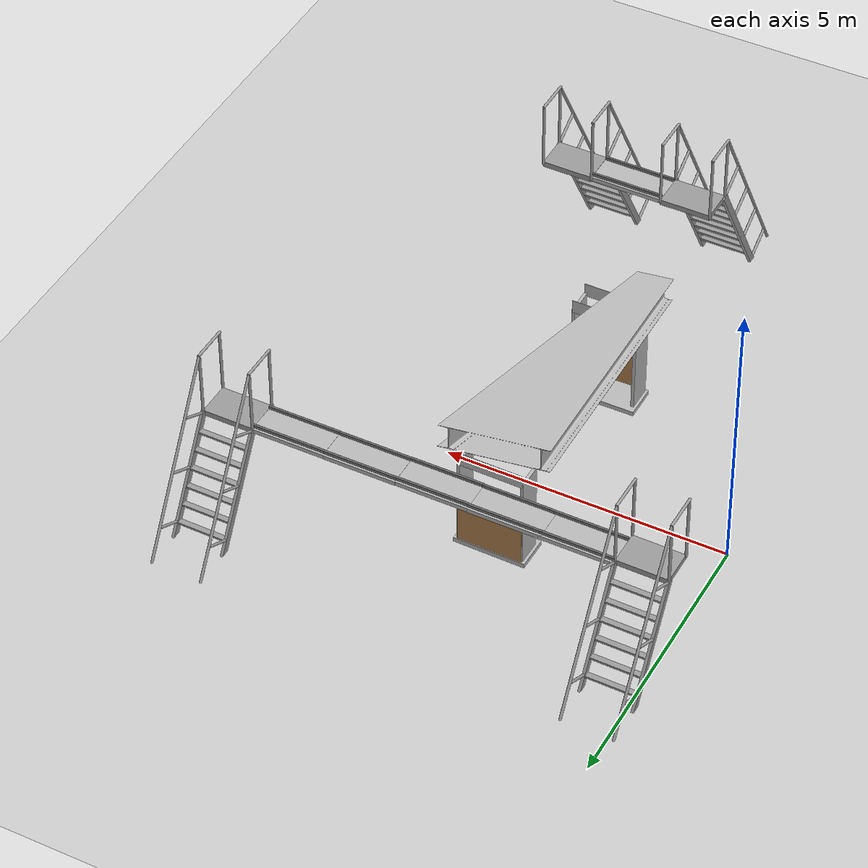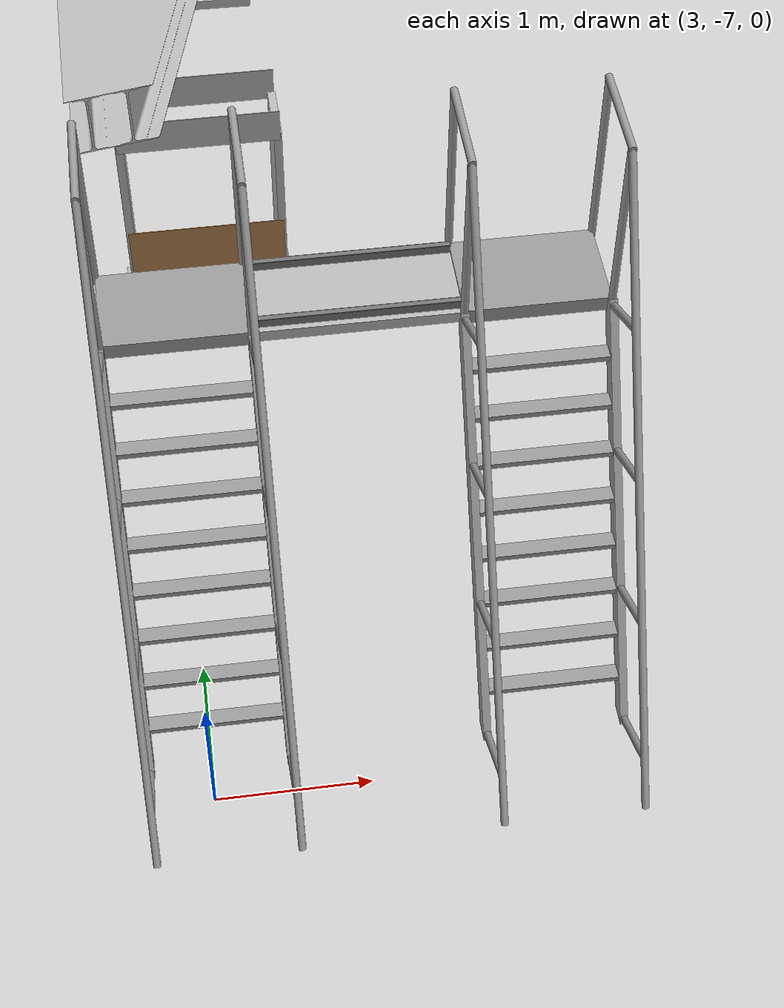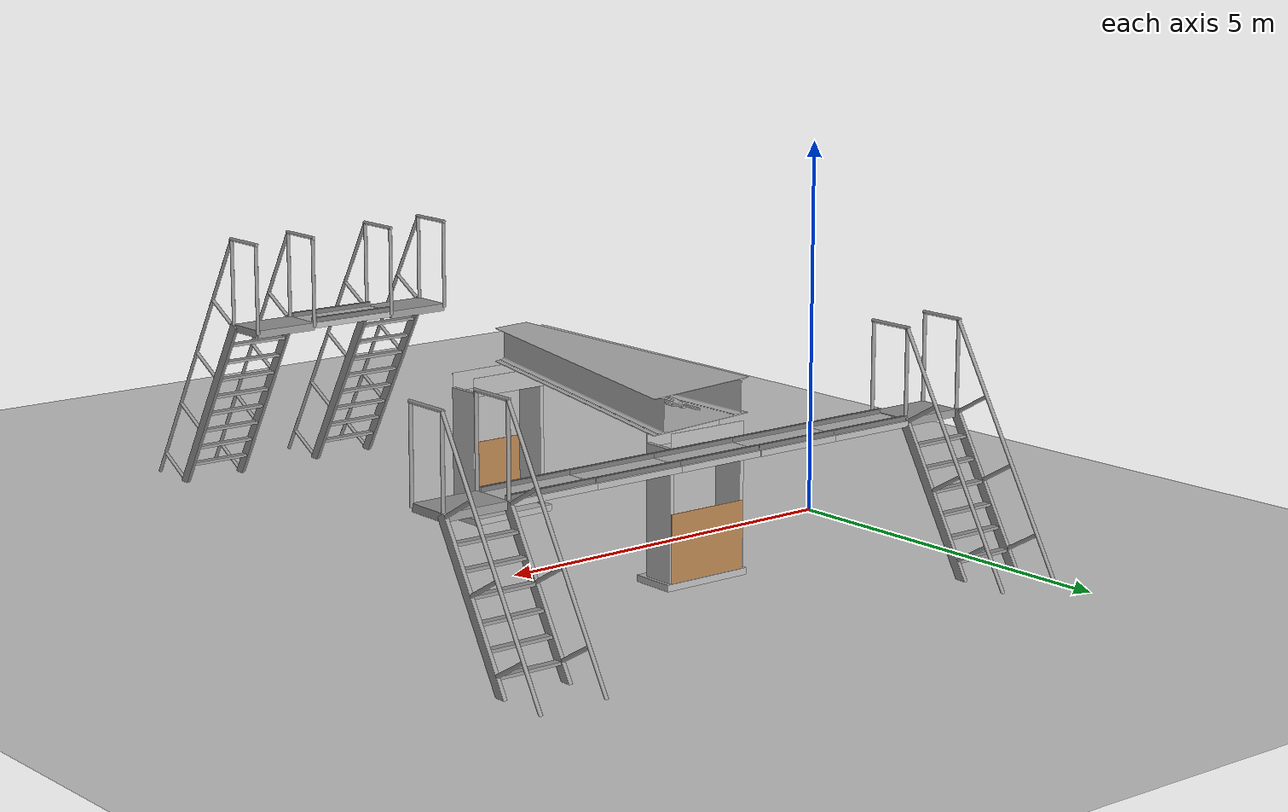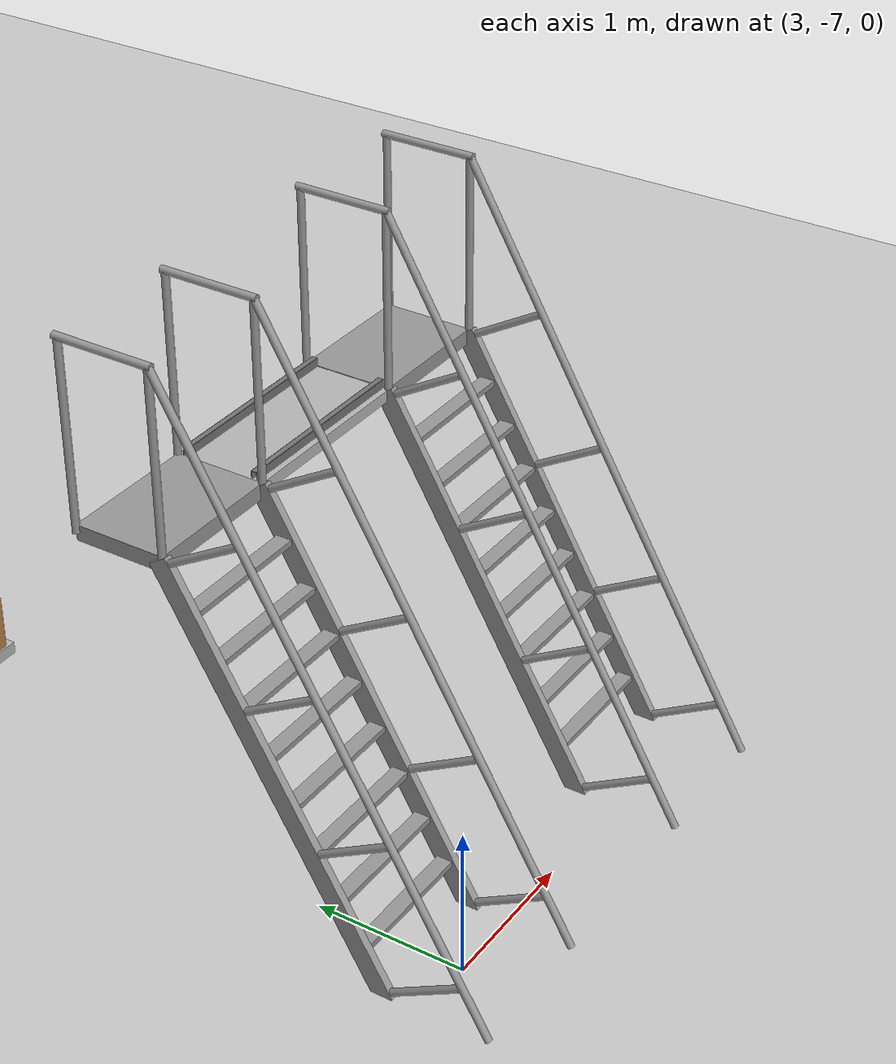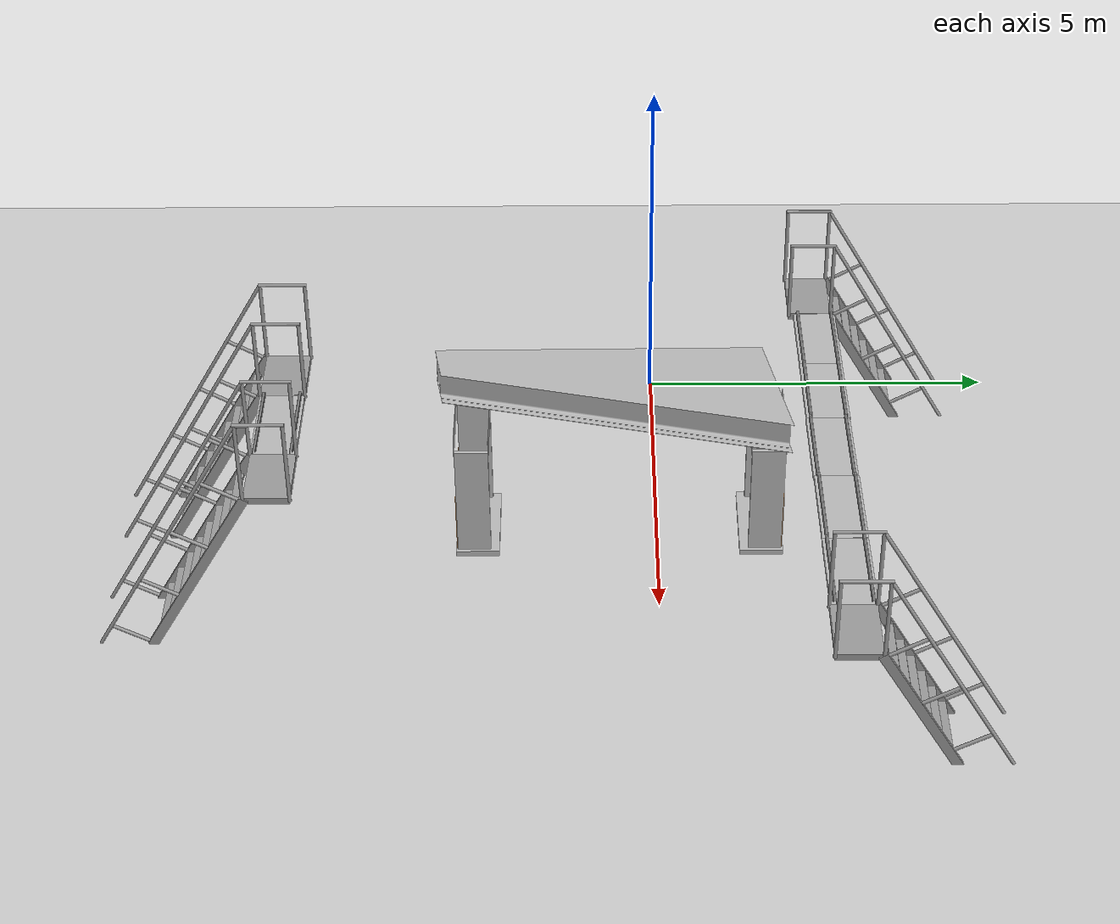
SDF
<sdf version="1.6">
 <world name="default">
  <light name="sun" type="directional">
   <pose>0 0 10 0 -0 0</pose>
   <diffuse>0.8 0.8 0.8 1</diffuse>
   <specular>0.2 0.2 0.2 1</specular>
   <attenuation>
    <range>1000</range>
    <constant>0.9</constant>
    <linear>0.01</linear>
    <quadratic>0.001</quadratic>
   </attenuation>
   <direction>-0.5 0.1 -0.9</direction>
  </light>
  <model name="ground_plane">
   <static>1</static>
   <link name="link">
    <collision name="collision">
     <geometry><plane><normal>0 0 1</normal><size>100 100</size></plane></geometry>
     <surface>
      <contact><collide_bitmask>65535</collide_bitmask></contact>
      <friction><ode><mu>100</mu><mu2>50</mu2></ode></friction>
     </surface>
    </collision>
    <visual name="visual">
     <cast_shadows>0</cast_shadows>
     <geometry><plane><normal>0 0 1</normal><size>100 100</size></plane></geometry>
     <material>
      <script><uri>file://media/materials/scripts/gazebo.material</uri><name>Gazebo/Grey</name></script>
     </material>
    </visual>
   </link>
  </model>
  <gravity>0 0 -9.8</gravity>
  <magnetic_field>6e-06 2.3e-05 -4.2e-05</magnetic_field>
  <atmosphere type="adiabatic"/>
  <physics name="default_physics" default="0" type="ode">
   <max_step_size>0.001</max_step_size>
   <real_time_factor>1</real_time_factor>
   <real_time_update_rate>1000</real_time_update_rate>
  </physics>
  <scene><ambient>0.4 0.4 0.4 1</ambient><background>0.7 0.7 0.7 1</background><shadows>1</shadows></scene>
  <spherical_coordinates>
   <surface_model>EARTH_WGS84</surface_model>
   <latitude_deg>0</latitude_deg>
   <longitude_deg>0</longitude_deg>
   <elevation>0</elevation>
   <heading_deg>0</heading_deg>
  </spherical_coordinates>
  <model name="ladder_60deg_2rails">
   <static>1</static>
   <link name="step0">
    <pose>0 0.15396 0.266667 0 -0 0</pose>
    <inertial>
     <mass>9.75482</mass>
     <inertia>
      <ixx>0.00957124</ixx>
      <iyy>0.65963</iyy>
      <izz>0.666842</izz>
      <ixy>0</ixy>
      <ixz>0</ixz>
      <iyz>0</iyz>
     </inertia>
    </inertial>
    <collision name="collision"><geometry><box><size>0.9 0.1016 0.0381</size></box></geometry></collision>
    <visual name="visual">
     <geometry><box><size>0.9 0.1016 0.0381</size></box></geometry>
     <material>
      <script><uri>file://media/materials/scripts/gazebo.material</uri><name>Gazebo/Grey</name></script>
     </material>
    </visual>
   </link>
   <link name="step1">
    <pose>0 0.30792 0.533333 0 -0 0</pose>
    <inertial>
     <mass>9.75482</mass>
     <inertia>
      <ixx>0.00957124</ixx>
      <iyy>0.65963</iyy>
      <izz>0.666842</izz>
      <ixy>0</ixy>
      <ixz>0</ixz>
      <iyz>0</iyz>
     </inertia>
    </inertial>
    <collision name="collision"><geometry><box><size>0.9 0.1016 0.0381</size></box></geometry></collision>
    <visual name="visual">
     <geometry><box><size>0.9 0.1016 0.0381</size></box></geometry>
     <material>
      <script><uri>file://media/materials/scripts/gazebo.material</uri><name>Gazebo/Grey</name></script>
     </material>
    </visual>
   </link>
   <link name="step2">
    <pose>0 0.46188 0.8 0 -0 0</pose>
    <inertial>
     <mass>9.75482</mass>
     <inertia>
      <ixx>0.00957124</ixx>
      <iyy>0.65963</iyy>
      <izz>0.666842</izz>
      <ixy>0</ixy>
      <ixz>0</ixz>
      <iyz>0</iyz>
     </inertia>
    </inertial>
    <collision name="collision"><geometry><box><size>0.9 0.1016 0.0381</size></box></geometry></collision>
    <visual name="visual">
     <geometry><box><size>0.9 0.1016 0.0381</size></box></geometry>
     <material>
      <script><uri>file://media/materials/scripts/gazebo.material</uri><name>Gazebo/Grey</name></script>
     </material>
    </visual>
   </link>
   <link name="step3">
    <pose>0 0.61584 1.06667 0 -0 0</pose>
    <inertial>
     <mass>9.75482</mass>
     <inertia>
      <ixx>0.00957124</ixx>
      <iyy>0.65963</iyy>
      <izz>0.666842</izz>
      <ixy>0</ixy>
      <ixz>0</ixz>
      <iyz>0</iyz>
     </inertia>
    </inertial>
    <collision name="collision"><geometry><box><size>0.9 0.1016 0.0381</size></box></geometry></collision>
    <visual name="visual">
     <geometry><box><size>0.9 0.1016 0.0381</size></box></geometry>
     <material>
      <script><uri>file://media/materials/scripts/gazebo.material</uri><name>Gazebo/Grey</name></script>
     </material>
    </visual>
   </link>
   <link name="step4">
    <pose>0 0.7698 1.33333 0 -0 0</pose>
    <inertial>
     <mass>9.75482</mass>
     <inertia>
      <ixx>0.00957124</ixx>
      <iyy>0.65963</iyy>
      <izz>0.666842</izz>
      <ixy>0</ixy>
      <ixz>0</ixz>
      <iyz>0</iyz>
     </inertia>
    </inertial>
    <collision name="collision"><geometry><box><size>0.9 0.1016 0.0381</size></box></geometry></collision>
    <visual name="visual">
     <geometry><box><size>0.9 0.1016 0.0381</size></box></geometry>
     <material>
      <script><uri>file://media/materials/scripts/gazebo.material</uri><name>Gazebo/Grey</name></script>
     </material>
    </visual>
   </link>
   <link name="step5">
    <pose>0 0.92376 1.6 0 -0 0</pose>
    <inertial>
     <mass>9.75482</mass>
     <inertia>
      <ixx>0.00957124</ixx>
      <iyy>0.65963</iyy>
      <izz>0.666842</izz>
      <ixy>0</ixy>
      <ixz>0</ixz>
      <iyz>0</iyz>
     </inertia>
    </inertial>
    <collision name="collision"><geometry><box><size>0.9 0.1016 0.0381</size></box></geometry></collision>
    <visual name="visual">
     <geometry><box><size>0.9 0.1016 0.0381</size></box></geometry>
     <material>
      <script><uri>file://media/materials/scripts/gazebo.material</uri><name>Gazebo/Grey</name></script>
     </material>
    </visual>
   </link>
   <link name="step6">
    <pose>0 1.07772 1.86667 0 -0 0</pose>
    <inertial>
     <mass>9.75482</mass>
     <inertia>
      <ixx>0.00957124</ixx>
      <iyy>0.65963</iyy>
      <izz>0.666842</izz>
      <ixy>0</ixy>
      <ixz>0</ixz>
      <iyz>0</iyz>
     </inertia>
    </inertial>
    <collision name="collision"><geometry><box><size>0.9 0.1016 0.0381</size></box></geometry></collision>
    <visual name="visual">
     <geometry><box><size>0.9 0.1016 0.0381</size></box></geometry>
     <material>
      <script><uri>file://media/materials/scripts/gazebo.material</uri><name>Gazebo/Grey</name></script>
     </material>
    </visual>
   </link>
   <link name="step7">
    <pose>0 1.23168 2.13333 0 -0 0</pose>
    <inertial>
     <mass>9.75482</mass>
     <inertia>
      <ixx>0.00957124</ixx>
      <iyy>0.65963</iyy>
      <izz>0.666842</izz>
      <ixy>0</ixy>
      <ixz>0</ixz>
      <iyz>0</iyz>
     </inertia>
    </inertial>
    <collision name="collision"><geometry><box><size>0.9 0.1016 0.0381</size></box></geometry></collision>
    <visual name="visual">
     <geometry><box><size>0.9 0.1016 0.0381</size></box></geometry>
     <material>
      <script><uri>file://media/materials/scripts/gazebo.material</uri><name>Gazebo/Grey</name></script>
     </material>
    </visual>
   </link>
   <link name="landing">
    <pose>0 1.68564 2.4 0 -0 0</pose>
    <inertial>
     <mass>57.6072</mass>
     <inertia><ixx>1.73518</ixx><iyy>3.89545</iyy><izz>5.6167</izz><ixy>0</ixy><ixz>0</ixz><iyz>0</iyz></inertia>
    </inertial>
    <collision name="collision"><geometry><box><size>0.9 0.6 0.1016</size></box></geometry></collision>
    <visual name="visual">
     <geometry><box><size>0.9 0.6 0.1016</size></box></geometry>
     <material>
      <script><uri>file://media/materials/scripts/gazebo.material</uri><name>Gazebo/Grey</name></script>
     </material>
    </visual>
   </link>
   <link name="left_side_wall">
    <pose>-0.45 0.69282 1.2 1.0472 -0 0</pose>
    <collision name="collision"><geometry><box><size>0.0508 2.85128 0.13</size></box></geometry></collision>
    <visual name="visual">
     <geometry><box><size>0.0508 2.85128 0.13</size></box></geometry>
     <material>
      <script><uri>file://media/materials/scripts/gazebo.material</uri><name>Gazebo/Grey</name></script>
     </material>
    </visual>
   </link>
   <link name="right_side_wall">
    <pose>0.45 0.69282 1.2 1.0472 -0 0</pose>
    <collision name="collision"><geometry><box><size>0.0508 2.85128 0.13</size></box></geometry></collision>
    <visual name="visual">
     <geometry><box><size>0.0508 2.85128 0.13</size></box></geometry>
     <material>
      <script><uri>file://media/materials/scripts/gazebo.material</uri><name>Gazebo/Grey</name></script>
     </material>
    </visual>
   </link>
   <link name="left_railing_long">
    <pose>-0.45 0.34282 1.80622 -0.523599 0 0</pose>
    <collision name="collision">
     <geometry><cylinder><radius>0.02413</radius><length>4.17128</length></cylinder></geometry>
    </collision>
    <visual name="visual">
     <geometry><cylinder><radius>0.02413</radius><length>4.17128</length></cylinder></geometry>
     <material>
      <script><uri>file://media/materials/scripts/gazebo.material</uri><name>Gazebo/Grey</name></script>
     </material>
    </visual>
   </link>
   <link name="left_railing_upright0">
    <pose>-0.45 -0.274963 0.15875 1.0472 -0 0</pose>
    <collision name="collision">
     <geometry><cylinder><radius>0.02413</radius><length>0.541218</length></cylinder></geometry>
    </collision>
    <visual name="visual">
     <geometry><cylinder><radius>0.02413</radius><length>0.541218</length></cylinder></geometry>
     <material>
      <script><uri>file://media/materials/scripts/gazebo.material</uri><name>Gazebo/Grey</name></script>
     </material>
    </visual>
   </link>
   <link name="left_railing_upright1">
    <pose>-0.45 0.186917 0.95875 1.0472 -0 0</pose>
    <collision name="collision">
     <geometry><cylinder><radius>0.02413</radius><length>0.541218</length></cylinder></geometry>
    </collision>
    <visual name="visual">
     <geometry><cylinder><radius>0.02413</radius><length>0.541218</length></cylinder></geometry>
     <material>
      <script><uri>file://media/materials/scripts/gazebo.material</uri><name>Gazebo/Grey</name></script>
     </material>
    </visual>
   </link>
   <link name="left_railing_upright2">
    <pose>-0.45 0.648797 1.75875 1.0472 -0 0</pose>
    <collision name="collision">
     <geometry><cylinder><radius>0.02413</radius><length>0.541218</length></cylinder></geometry>
    </collision>
    <visual name="visual">
     <geometry><cylinder><radius>0.02413</radius><length>0.541218</length></cylinder></geometry>
     <material>
      <script><uri>file://media/materials/scripts/gazebo.material</uri><name>Gazebo/Grey</name></script>
     </material>
    </visual>
   </link>
   <link name="left_railing_upright3">
    <pose>-0.45 1.11068 2.55875 1.0472 -0 0</pose>
    <collision name="collision">
     <geometry><cylinder><radius>0.02413</radius><length>0.541218</length></cylinder></geometry>
    </collision>
    <visual name="visual">
     <geometry><cylinder><radius>0.02413</radius><length>0.541218</length></cylinder></geometry>
     <material>
      <script><uri>file://media/materials/scripts/gazebo.material</uri><name>Gazebo/Grey</name></script>
     </material>
    </visual>
   </link>
   <link name="left_railing_landing_top">
    <pose>-0.45 1.68564 3.61244 1.5708 -0 0</pose>
    <collision name="collision">
     <geometry><cylinder><radius>0.02413</radius><length>0.64826</length></cylinder></geometry>
    </collision>
    <visual name="visual">
     <geometry><cylinder><radius>0.02413</radius><length>0.64826</length></cylinder></geometry>
     <material>
      <script><uri>file://media/materials/scripts/gazebo.material</uri><name>Gazebo/Grey</name></script>
     </material>
    </visual>
   </link>
   <link name="left_railing_landing_upright_0">
    <pose>-0.45 1.38564 3.00622 0 -0 0</pose>
    <collision name="collision">
     <geometry><cylinder><radius>0.02413</radius><length>1.21244</length></cylinder></geometry>
    </collision>
    <visual name="visual">
     <geometry><cylinder><radius>0.02413</radius><length>1.21244</length></cylinder></geometry>
     <material>
      <script><uri>file://media/materials/scripts/gazebo.material</uri><name>Gazebo/Grey</name></script>
     </material>
    </visual>
   </link>
   <link name="left_railing_landing_upright_1">
    <pose>-0.45 1.98564 3.00622 0 -0 0</pose>
    <collision name="collision">
     <geometry><cylinder><radius>0.02413</radius><length>1.21244</length></cylinder></geometry>
    </collision>
    <visual name="visual">
     <geometry><cylinder><radius>0.02413</radius><length>1.21244</length></cylinder></geometry>
     <material>
      <script><uri>file://media/materials/scripts/gazebo.material</uri><name>Gazebo/Grey</name></script>
     </material>
    </visual>
   </link>
   <link name="right_railing_long">
    <pose>0.45 0.34282 1.80622 -0.523599 0 0</pose>
    <collision name="collision">
     <geometry><cylinder><radius>0.02413</radius><length>4.17128</length></cylinder></geometry>
    </collision>
    <visual name="visual">
     <geometry><cylinder><radius>0.02413</radius><length>4.17128</length></cylinder></geometry>
     <material>
      <script><uri>file://media/materials/scripts/gazebo.material</uri><name>Gazebo/Grey</name></script>
     </material>
    </visual>
   </link>
   <link name="right_railing_upright0">
    <pose>0.45 -0.274963 0.15875 1.0472 -0 0</pose>
    <collision name="collision">
     <geometry><cylinder><radius>0.02413</radius><length>0.541218</length></cylinder></geometry>
    </collision>
    <visual name="visual">
     <geometry><cylinder><radius>0.02413</radius><length>0.541218</length></cylinder></geometry>
     <material>
      <script><uri>file://media/materials/scripts/gazebo.material</uri><name>Gazebo/Grey</name></script>
     </material>
    </visual>
   </link>
   <link name="right_railing_upright1">
    <pose>0.45 0.186917 0.95875 1.0472 -0 0</pose>
    <collision name="collision">
     <geometry><cylinder><radius>0.02413</radius><length>0.541218</length></cylinder></geometry>
    </collision>
    <visual name="visual">
     <geometry><cylinder><radius>0.02413</radius><length>0.541218</length></cylinder></geometry>
     <material>
      <script><uri>file://media/materials/scripts/gazebo.material</uri><name>Gazebo/Grey</name></script>
     </material>
    </visual>
   </link>
   <link name="right_railing_upright2">
    <pose>0.45 0.648797 1.75875 1.0472 -0 0</pose>
    <collision name="collision">
     <geometry><cylinder><radius>0.02413</radius><length>0.541218</length></cylinder></geometry>
    </collision>
    <visual name="visual">
     <geometry><cylinder><radius>0.02413</radius><length>0.541218</length></cylinder></geometry>
     <material>
      <script><uri>file://media/materials/scripts/gazebo.material</uri><name>Gazebo/Grey</name></script>
     </material>
    </visual>
   </link>
   <link name="right_railing_upright3">
    <pose>0.45 1.11068 2.55875 1.0472 -0 0</pose>
    <collision name="collision">
     <geometry><cylinder><radius>0.02413</radius><length>0.541218</length></cylinder></geometry>
    </collision>
    <visual name="visual">
     <geometry><cylinder><radius>0.02413</radius><length>0.541218</length></cylinder></geometry>
     <material>
      <script><uri>file://media/materials/scripts/gazebo.material</uri><name>Gazebo/Grey</name></script>
     </material>
    </visual>
   </link>
   <link name="right_railing_landing_top">
    <pose>0.45 1.68564 3.61244 1.5708 -0 0</pose>
    <collision name="collision">
     <geometry><cylinder><radius>0.02413</radius><length>0.64826</length></cylinder></geometry>
    </collision>
    <visual name="visual">
     <geometry><cylinder><radius>0.02413</radius><length>0.64826</length></cylinder></geometry>
     <material>
      <script><uri>file://media/materials/scripts/gazebo.material</uri><name>Gazebo/Grey</name></script>
     </material>
    </visual>
   </link>
   <link name="right_railing_landing_upright_0">
    <pose>0.45 1.38564 3.00622 0 -0 0</pose>
    <collision name="collision">
     <geometry><cylinder><radius>0.02413</radius><length>1.21244</length></cylinder></geometry>
    </collision>
    <visual name="visual">
     <geometry><cylinder><radius>0.02413</radius><length>1.21244</length></cylinder></geometry>
     <material>
      <script><uri>file://media/materials/scripts/gazebo.material</uri><name>Gazebo/Grey</name></script>
     </material>
    </visual>
   </link>
   <link name="right_railing_landing_upright_1">
    <pose>0.45 1.98564 3.00622 0 -0 0</pose>
    <collision name="collision">
     <geometry><cylinder><radius>0.02413</radius><length>1.21244</length></cylinder></geometry>
    </collision>
    <visual name="visual">
     <geometry><cylinder><radius>0.02413</radius><length>1.21244</length></cylinder></geometry>
     <material>
      <script><uri>file://media/materials/scripts/gazebo.material</uri><name>Gazebo/Grey</name></script>
     </material>
    </visual>
   </link>
   <pose>5.22759 -6.71904 0 0 -0 0</pose>
  </model>
  <model name="ladder_60deg_2rails_clone">
   <static>1</static>
   <link name="step0">
    <pose>0 0.15396 0.266667 0 -0 0</pose>
    <inertial>
     <mass>9.75482</mass>
     <inertia>
      <ixx>0.00957124</ixx>
      <iyy>0.65963</iyy>
      <izz>0.666842</izz>
      <ixy>0</ixy>
      <ixz>0</ixz>
      <iyz>0</iyz>
     </inertia>
    </inertial>
    <collision name="collision"><geometry><box><size>0.9 0.1016 0.0381</size></box></geometry></collision>
    <visual name="visual">
     <geometry><box><size>0.9 0.1016 0.0381</size></box></geometry>
     <material>
      <script><uri>file://media/materials/scripts/gazebo.material</uri><name>Gazebo/Grey</name></script>
     </material>
    </visual>
   </link>
   <link name="step1">
    <pose>0 0.30792 0.533333 0 -0 0</pose>
    <inertial>
     <mass>9.75482</mass>
     <inertia>
      <ixx>0.00957124</ixx>
      <iyy>0.65963</iyy>
      <izz>0.666842</izz>
      <ixy>0</ixy>
      <ixz>0</ixz>
      <iyz>0</iyz>
     </inertia>
    </inertial>
    <collision name="collision"><geometry><box><size>0.9 0.1016 0.0381</size></box></geometry></collision>
    <visual name="visual">
     <geometry><box><size>0.9 0.1016 0.0381</size></box></geometry>
     <material>
      <script><uri>file://media/materials/scripts/gazebo.material</uri><name>Gazebo/Grey</name></script>
     </material>
    </visual>
   </link>
   <link name="step2">
    <pose>0 0.46188 0.8 0 -0 0</pose>
    <inertial>
     <mass>9.75482</mass>
     <inertia>
      <ixx>0.00957124</ixx>
      <iyy>0.65963</iyy>
      <izz>0.666842</izz>
      <ixy>0</ixy>
      <ixz>0</ixz>
      <iyz>0</iyz>
     </inertia>
    </inertial>
    <collision name="collision"><geometry><box><size>0.9 0.1016 0.0381</size></box></geometry></collision>
    <visual name="visual">
     <geometry><box><size>0.9 0.1016 0.0381</size></box></geometry>
     <material>
      <script><uri>file://media/materials/scripts/gazebo.material</uri><name>Gazebo/Grey</name></script>
     </material>
    </visual>
   </link>
   <link name="step3">
    <pose>0 0.61584 1.06667 0 -0 0</pose>
    <inertial>
     <mass>9.75482</mass>
     <inertia>
      <ixx>0.00957124</ixx>
      <iyy>0.65963</iyy>
      <izz>0.666842</izz>
      <ixy>0</ixy>
      <ixz>0</ixz>
      <iyz>0</iyz>
     </inertia>
    </inertial>
    <collision name="collision"><geometry><box><size>0.9 0.1016 0.0381</size></box></geometry></collision>
    <visual name="visual">
     <geometry><box><size>0.9 0.1016 0.0381</size></box></geometry>
     <material>
      <script><uri>file://media/materials/scripts/gazebo.material</uri><name>Gazebo/Grey</name></script>
     </material>
    </visual>
   </link>
   <link name="step4">
    <pose>0 0.7698 1.33333 0 -0 0</pose>
    <inertial>
     <mass>9.75482</mass>
     <inertia>
      <ixx>0.00957124</ixx>
      <iyy>0.65963</iyy>
      <izz>0.666842</izz>
      <ixy>0</ixy>
      <ixz>0</ixz>
      <iyz>0</iyz>
     </inertia>
    </inertial>
    <collision name="collision"><geometry><box><size>0.9 0.1016 0.0381</size></box></geometry></collision>
    <visual name="visual">
     <geometry><box><size>0.9 0.1016 0.0381</size></box></geometry>
     <material>
      <script><uri>file://media/materials/scripts/gazebo.material</uri><name>Gazebo/Grey</name></script>
     </material>
    </visual>
   </link>
   <link name="step5">
    <pose>0 0.92376 1.6 0 -0 0</pose>
    <inertial>
     <mass>9.75482</mass>
     <inertia>
      <ixx>0.00957124</ixx>
      <iyy>0.65963</iyy>
      <izz>0.666842</izz>
      <ixy>0</ixy>
      <ixz>0</ixz>
      <iyz>0</iyz>
     </inertia>
    </inertial>
    <collision name="collision"><geometry><box><size>0.9 0.1016 0.0381</size></box></geometry></collision>
    <visual name="visual">
     <geometry><box><size>0.9 0.1016 0.0381</size></box></geometry>
     <material>
      <script><uri>file://media/materials/scripts/gazebo.material</uri><name>Gazebo/Grey</name></script>
     </material>
    </visual>
   </link>
   <link name="step6">
    <pose>0 1.07772 1.86667 0 -0 0</pose>
    <inertial>
     <mass>9.75482</mass>
     <inertia>
      <ixx>0.00957124</ixx>
      <iyy>0.65963</iyy>
      <izz>0.666842</izz>
      <ixy>0</ixy>
      <ixz>0</ixz>
      <iyz>0</iyz>
     </inertia>
    </inertial>
    <collision name="collision"><geometry><box><size>0.9 0.1016 0.0381</size></box></geometry></collision>
    <visual name="visual">
     <geometry><box><size>0.9 0.1016 0.0381</size></box></geometry>
     <material>
      <script><uri>file://media/materials/scripts/gazebo.material</uri><name>Gazebo/Grey</name></script>
     </material>
    </visual>
   </link>
   <link name="step7">
    <pose>0 1.23168 2.13333 0 -0 0</pose>
    <inertial>
     <mass>9.75482</mass>
     <inertia>
      <ixx>0.00957124</ixx>
      <iyy>0.65963</iyy>
      <izz>0.666842</izz>
      <ixy>0</ixy>
      <ixz>0</ixz>
      <iyz>0</iyz>
     </inertia>
    </inertial>
    <collision name="collision"><geometry><box><size>0.9 0.1016 0.0381</size></box></geometry></collision>
    <visual name="visual">
     <geometry><box><size>0.9 0.1016 0.0381</size></box></geometry>
     <material>
      <script><uri>file://media/materials/scripts/gazebo.material</uri><name>Gazebo/Grey</name></script>
     </material>
    </visual>
   </link>
   <link name="landing">
    <pose>0 1.68564 2.4 0 -0 0</pose>
    <inertial>
     <mass>57.6072</mass>
     <inertia><ixx>1.73518</ixx><iyy>3.89545</iyy><izz>5.6167</izz><ixy>0</ixy><ixz>0</ixz><iyz>0</iyz></inertia>
    </inertial>
    <collision name="collision"><geometry><box><size>0.9 0.6 0.1016</size></box></geometry></collision>
    <visual name="visual">
     <geometry><box><size>0.9 0.6 0.1016</size></box></geometry>
     <material>
      <script><uri>file://media/materials/scripts/gazebo.material</uri><name>Gazebo/Grey</name></script>
     </material>
    </visual>
   </link>
   <link name="left_side_wall">
    <pose>-0.45 0.69282 1.2 1.0472 -0 0</pose>
    <collision name="collision"><geometry><box><size>0.0508 2.85128 0.13</size></box></geometry></collision>
    <visual name="visual">
     <geometry><box><size>0.0508 2.85128 0.13</size></box></geometry>
     <material>
      <script><uri>file://media/materials/scripts/gazebo.material</uri><name>Gazebo/Grey</name></script>
     </material>
    </visual>
   </link>
   <link name="right_side_wall">
    <pose>0.45 0.69282 1.2 1.0472 -0 0</pose>
    <collision name="collision"><geometry><box><size>0.0508 2.85128 0.13</size></box></geometry></collision>
    <visual name="visual">
     <geometry><box><size>0.0508 2.85128 0.13</size></box></geometry>
     <material>
      <script><uri>file://media/materials/scripts/gazebo.material</uri><name>Gazebo/Grey</name></script>
     </material>
    </visual>
   </link>
   <link name="left_railing_long">
    <pose>-0.45 0.34282 1.80622 -0.523599 0 0</pose>
    <collision name="collision">
     <geometry><cylinder><radius>0.02413</radius><length>4.17128</length></cylinder></geometry>
    </collision>
    <visual name="visual">
     <geometry><cylinder><radius>0.02413</radius><length>4.17128</length></cylinder></geometry>
     <material>
      <script><uri>file://media/materials/scripts/gazebo.material</uri><name>Gazebo/Grey</name></script>
     </material>
    </visual>
   </link>
   <link name="left_railing_upright0">
    <pose>-0.45 -0.274963 0.15875 1.0472 -0 0</pose>
    <collision name="collision">
     <geometry><cylinder><radius>0.02413</radius><length>0.541218</length></cylinder></geometry>
    </collision>
    <visual name="visual">
     <geometry><cylinder><radius>0.02413</radius><length>0.541218</length></cylinder></geometry>
     <material>
      <script><uri>file://media/materials/scripts/gazebo.material</uri><name>Gazebo/Grey</name></script>
     </material>
    </visual>
   </link>
   <link name="left_railing_upright1">
    <pose>-0.45 0.186917 0.95875 1.0472 -0 0</pose>
    <collision name="collision">
     <geometry><cylinder><radius>0.02413</radius><length>0.541218</length></cylinder></geometry>
    </collision>
    <visual name="visual">
     <geometry><cylinder><radius>0.02413</radius><length>0.541218</length></cylinder></geometry>
     <material>
      <script><uri>file://media/materials/scripts/gazebo.material</uri><name>Gazebo/Grey</name></script>
     </material>
    </visual>
   </link>
   <link name="left_railing_upright2">
    <pose>-0.45 0.648797 1.75875 1.0472 -0 0</pose>
    <collision name="collision">
     <geometry><cylinder><radius>0.02413</radius><length>0.541218</length></cylinder></geometry>
    </collision>
    <visual name="visual">
     <geometry><cylinder><radius>0.02413</radius><length>0.541218</length></cylinder></geometry>
     <material>
      <script><uri>file://media/materials/scripts/gazebo.material</uri><name>Gazebo/Grey</name></script>
     </material>
    </visual>
   </link>
   <link name="left_railing_upright3">
    <pose>-0.45 1.11068 2.55875 1.0472 -0 0</pose>
    <collision name="collision">
     <geometry><cylinder><radius>0.02413</radius><length>0.541218</length></cylinder></geometry>
    </collision>
    <visual name="visual">
     <geometry><cylinder><radius>0.02413</radius><length>0.541218</length></cylinder></geometry>
     <material>
      <script><uri>file://media/materials/scripts/gazebo.material</uri><name>Gazebo/Grey</name></script>
     </material>
    </visual>
   </link>
   <link name="left_railing_landing_top">
    <pose>-0.45 1.68564 3.61244 1.5708 -0 0</pose>
    <collision name="collision">
     <geometry><cylinder><radius>0.02413</radius><length>0.64826</length></cylinder></geometry>
    </collision>
    <visual name="visual">
     <geometry><cylinder><radius>0.02413</radius><length>0.64826</length></cylinder></geometry>
     <material>
      <script><uri>file://media/materials/scripts/gazebo.material</uri><name>Gazebo/Grey</name></script>
     </material>
    </visual>
   </link>
   <link name="left_railing_landing_upright_0">
    <pose>-0.45 1.38564 3.00622 0 -0 0</pose>
    <collision name="collision">
     <geometry><cylinder><radius>0.02413</radius><length>1.21244</length></cylinder></geometry>
    </collision>
    <visual name="visual">
     <geometry><cylinder><radius>0.02413</radius><length>1.21244</length></cylinder></geometry>
     <material>
      <script><uri>file://media/materials/scripts/gazebo.material</uri><name>Gazebo/Grey</name></script>
     </material>
    </visual>
   </link>
   <link name="left_railing_landing_upright_1">
    <pose>-0.45 1.98564 3.00622 0 -0 0</pose>
    <collision name="collision">
     <geometry><cylinder><radius>0.02413</radius><length>1.21244</length></cylinder></geometry>
    </collision>
    <visual name="visual">
     <geometry><cylinder><radius>0.02413</radius><length>1.21244</length></cylinder></geometry>
     <material>
      <script><uri>file://media/materials/scripts/gazebo.material</uri><name>Gazebo/Grey</name></script>
     </material>
    </visual>
   </link>
   <link name="right_railing_long">
    <pose>0.45 0.34282 1.80622 -0.523599 0 0</pose>
    <collision name="collision">
     <geometry><cylinder><radius>0.02413</radius><length>4.17128</length></cylinder></geometry>
    </collision>
    <visual name="visual">
     <geometry><cylinder><radius>0.02413</radius><length>4.17128</length></cylinder></geometry>
     <material>
      <script><uri>file://media/materials/scripts/gazebo.material</uri><name>Gazebo/Grey</name></script>
     </material>
    </visual>
   </link>
   <link name="right_railing_upright0">
    <pose>0.45 -0.274963 0.15875 1.0472 -0 0</pose>
    <collision name="collision">
     <geometry><cylinder><radius>0.02413</radius><length>0.541218</length></cylinder></geometry>
    </collision>
    <visual name="visual">
     <geometry><cylinder><radius>0.02413</radius><length>0.541218</length></cylinder></geometry>
     <material>
      <script><uri>file://media/materials/scripts/gazebo.material</uri><name>Gazebo/Grey</name></script>
     </material>
    </visual>
   </link>
   <link name="right_railing_upright1">
    <pose>0.45 0.186917 0.95875 1.0472 -0 0</pose>
    <collision name="collision">
     <geometry><cylinder><radius>0.02413</radius><length>0.541218</length></cylinder></geometry>
    </collision>
    <visual name="visual">
     <geometry><cylinder><radius>0.02413</radius><length>0.541218</length></cylinder></geometry>
     <material>
      <script><uri>file://media/materials/scripts/gazebo.material</uri><name>Gazebo/Grey</name></script>
     </material>
    </visual>
   </link>
   <link name="right_railing_upright2">
    <pose>0.45 0.648797 1.75875 1.0472 -0 0</pose>
    <collision name="collision">
     <geometry><cylinder><radius>0.02413</radius><length>0.541218</length></cylinder></geometry>
    </collision>
    <visual name="visual">
     <geometry><cylinder><radius>0.02413</radius><length>0.541218</length></cylinder></geometry>
     <material>
      <script><uri>file://media/materials/scripts/gazebo.material</uri><name>Gazebo/Grey</name></script>
     </material>
    </visual>
   </link>
   <link name="right_railing_upright3">
    <pose>0.45 1.11068 2.55875 1.0472 -0 0</pose>
    <collision name="collision">
     <geometry><cylinder><radius>0.02413</radius><length>0.541218</length></cylinder></geometry>
    </collision>
    <visual name="visual">
     <geometry><cylinder><radius>0.02413</radius><length>0.541218</length></cylinder></geometry>
     <material>
      <script><uri>file://media/materials/scripts/gazebo.material</uri><name>Gazebo/Grey</name></script>
     </material>
    </visual>
   </link>
   <link name="right_railing_landing_top">
    <pose>0.45 1.68564 3.61244 1.5708 -0 0</pose>
    <collision name="collision">
     <geometry><cylinder><radius>0.02413</radius><length>0.64826</length></cylinder></geometry>
    </collision>
    <visual name="visual">
     <geometry><cylinder><radius>0.02413</radius><length>0.64826</length></cylinder></geometry>
     <material>
      <script><uri>file://media/materials/scripts/gazebo.material</uri><name>Gazebo/Grey</name></script>
     </material>
    </visual>
   </link>
   <link name="right_railing_landing_upright_0">
    <pose>0.45 1.38564 3.00622 0 -0 0</pose>
    <collision name="collision">
     <geometry><cylinder><radius>0.02413</radius><length>1.21244</length></cylinder></geometry>
    </collision>
    <visual name="visual">
     <geometry><cylinder><radius>0.02413</radius><length>1.21244</length></cylinder></geometry>
     <material>
      <script><uri>file://media/materials/scripts/gazebo.material</uri><name>Gazebo/Grey</name></script>
     </material>
    </visual>
   </link>
   <link name="right_railing_landing_upright_1">
    <pose>0.45 1.98564 3.00622 0 -0 0</pose>
    <collision name="collision">
     <geometry><cylinder><radius>0.02413</radius><length>1.21244</length></cylinder></geometry>
    </collision>
    <visual name="visual">
     <geometry><cylinder><radius>0.02413</radius><length>1.21244</length></cylinder></geometry>
     <material>
      <script><uri>file://media/materials/scripts/gazebo.material</uri><name>Gazebo/Grey</name></script>
     </material>
    </visual>
   </link>
   <pose>7.53336 4.00092 -0.605235 0 -0 3.13335</pose>
  </model>
  <model name="ladder_60deg_2rails_clone_clone">
   <static>1</static>
   <link name="step0">
    <pose>0 0.15396 0.266667 0 -0 0</pose>
    <inertial>
     <mass>9.75482</mass>
     <inertia>
      <ixx>0.00957124</ixx>
      <iyy>0.65963</iyy>
      <izz>0.666842</izz>
      <ixy>0</ixy>
      <ixz>0</ixz>
      <iyz>0</iyz>
     </inertia>
    </inertial>
    <collision name="collision"><geometry><box><size>0.9 0.1016 0.0381</size></box></geometry></collision>
    <visual name="visual">
     <geometry><box><size>0.9 0.1016 0.0381</size></box></geometry>
     <material>
      <script><uri>file://media/materials/scripts/gazebo.material</uri><name>Gazebo/Grey</name></script>
     </material>
    </visual>
   </link>
   <link name="step1">
    <pose>0 0.30792 0.533333 0 -0 0</pose>
    <inertial>
     <mass>9.75482</mass>
     <inertia>
      <ixx>0.00957124</ixx>
      <iyy>0.65963</iyy>
      <izz>0.666842</izz>
      <ixy>0</ixy>
      <ixz>0</ixz>
      <iyz>0</iyz>
     </inertia>
    </inertial>
    <collision name="collision"><geometry><box><size>0.9 0.1016 0.0381</size></box></geometry></collision>
    <visual name="visual">
     <geometry><box><size>0.9 0.1016 0.0381</size></box></geometry>
     <material>
      <script><uri>file://media/materials/scripts/gazebo.material</uri><name>Gazebo/Grey</name></script>
     </material>
    </visual>
   </link>
   <link name="step2">
    <pose>0 0.46188 0.8 0 -0 0</pose>
    <inertial>
     <mass>9.75482</mass>
     <inertia>
      <ixx>0.00957124</ixx>
      <iyy>0.65963</iyy>
      <izz>0.666842</izz>
      <ixy>0</ixy>
      <ixz>0</ixz>
      <iyz>0</iyz>
     </inertia>
    </inertial>
    <collision name="collision"><geometry><box><size>0.9 0.1016 0.0381</size></box></geometry></collision>
    <visual name="visual">
     <geometry><box><size>0.9 0.1016 0.0381</size></box></geometry>
     <material>
      <script><uri>file://media/materials/scripts/gazebo.material</uri><name>Gazebo/Grey</name></script>
     </material>
    </visual>
   </link>
   <link name="step3">
    <pose>0 0.61584 1.06667 0 -0 0</pose>
    <inertial>
     <mass>9.75482</mass>
     <inertia>
      <ixx>0.00957124</ixx>
      <iyy>0.65963</iyy>
      <izz>0.666842</izz>
      <ixy>0</ixy>
      <ixz>0</ixz>
      <iyz>0</iyz>
     </inertia>
    </inertial>
    <collision name="collision"><geometry><box><size>0.9 0.1016 0.0381</size></box></geometry></collision>
    <visual name="visual">
     <geometry><box><size>0.9 0.1016 0.0381</size></box></geometry>
     <material>
      <script><uri>file://media/materials/scripts/gazebo.material</uri><name>Gazebo/Grey</name></script>
     </material>
    </visual>
   </link>
   <link name="step4">
    <pose>0 0.7698 1.33333 0 -0 0</pose>
    <inertial>
     <mass>9.75482</mass>
     <inertia>
      <ixx>0.00957124</ixx>
      <iyy>0.65963</iyy>
      <izz>0.666842</izz>
      <ixy>0</ixy>
      <ixz>0</ixz>
      <iyz>0</iyz>
     </inertia>
    </inertial>
    <collision name="collision"><geometry><box><size>0.9 0.1016 0.0381</size></box></geometry></collision>
    <visual name="visual">
     <geometry><box><size>0.9 0.1016 0.0381</size></box></geometry>
     <material>
      <script><uri>file://media/materials/scripts/gazebo.material</uri><name>Gazebo/Grey</name></script>
     </material>
    </visual>
   </link>
   <link name="step5">
    <pose>0 0.92376 1.6 0 -0 0</pose>
    <inertial>
     <mass>9.75482</mass>
     <inertia>
      <ixx>0.00957124</ixx>
      <iyy>0.65963</iyy>
      <izz>0.666842</izz>
      <ixy>0</ixy>
      <ixz>0</ixz>
      <iyz>0</iyz>
     </inertia>
    </inertial>
    <collision name="collision"><geometry><box><size>0.9 0.1016 0.0381</size></box></geometry></collision>
    <visual name="visual">
     <geometry><box><size>0.9 0.1016 0.0381</size></box></geometry>
     <material>
      <script><uri>file://media/materials/scripts/gazebo.material</uri><name>Gazebo/Grey</name></script>
     </material>
    </visual>
   </link>
   <link name="step6">
    <pose>0 1.07772 1.86667 0 -0 0</pose>
    <inertial>
     <mass>9.75482</mass>
     <inertia>
      <ixx>0.00957124</ixx>
      <iyy>0.65963</iyy>
      <izz>0.666842</izz>
      <ixy>0</ixy>
      <ixz>0</ixz>
      <iyz>0</iyz>
     </inertia>
    </inertial>
    <collision name="collision"><geometry><box><size>0.9 0.1016 0.0381</size></box></geometry></collision>
    <visual name="visual">
     <geometry><box><size>0.9 0.1016 0.0381</size></box></geometry>
     <material>
      <script><uri>file://media/materials/scripts/gazebo.material</uri><name>Gazebo/Grey</name></script>
     </material>
    </visual>
   </link>
   <link name="step7">
    <pose>0 1.23168 2.13333 0 -0 0</pose>
    <inertial>
     <mass>9.75482</mass>
     <inertia>
      <ixx>0.00957124</ixx>
      <iyy>0.65963</iyy>
      <izz>0.666842</izz>
      <ixy>0</ixy>
      <ixz>0</ixz>
      <iyz>0</iyz>
     </inertia>
    </inertial>
    <collision name="collision"><geometry><box><size>0.9 0.1016 0.0381</size></box></geometry></collision>
    <visual name="visual">
     <geometry><box><size>0.9 0.1016 0.0381</size></box></geometry>
     <material>
      <script><uri>file://media/materials/scripts/gazebo.material</uri><name>Gazebo/Grey</name></script>
     </material>
    </visual>
   </link>
   <link name="landing">
    <pose>0 1.68564 2.4 0 -0 0</pose>
    <inertial>
     <mass>57.6072</mass>
     <inertia><ixx>1.73518</ixx><iyy>3.89545</iyy><izz>5.6167</izz><ixy>0</ixy><ixz>0</ixz><iyz>0</iyz></inertia>
    </inertial>
    <collision name="collision"><geometry><box><size>0.9 0.6 0.1016</size></box></geometry></collision>
    <visual name="visual">
     <geometry><box><size>0.9 0.6 0.1016</size></box></geometry>
     <material>
      <script><uri>file://media/materials/scripts/gazebo.material</uri><name>Gazebo/Grey</name></script>
     </material>
    </visual>
   </link>
   <link name="left_side_wall">
    <pose>-0.45 0.69282 1.2 1.0472 -0 0</pose>
    <collision name="collision"><geometry><box><size>0.0508 2.85128 0.13</size></box></geometry></collision>
    <visual name="visual">
     <geometry><box><size>0.0508 2.85128 0.13</size></box></geometry>
     <material>
      <script><uri>file://media/materials/scripts/gazebo.material</uri><name>Gazebo/Grey</name></script>
     </material>
    </visual>
   </link>
   <link name="right_side_wall">
    <pose>0.45 0.69282 1.2 1.0472 -0 0</pose>
    <collision name="collision"><geometry><box><size>0.0508 2.85128 0.13</size></box></geometry></collision>
    <visual name="visual">
     <geometry><box><size>0.0508 2.85128 0.13</size></box></geometry>
     <material>
      <script><uri>file://media/materials/scripts/gazebo.material</uri><name>Gazebo/Grey</name></script>
     </material>
    </visual>
   </link>
   <link name="left_railing_long">
    <pose>-0.45 0.34282 1.80622 -0.523599 0 0</pose>
    <collision name="collision">
     <geometry><cylinder><radius>0.02413</radius><length>4.17128</length></cylinder></geometry>
    </collision>
    <visual name="visual">
     <geometry><cylinder><radius>0.02413</radius><length>4.17128</length></cylinder></geometry>
     <material>
      <script><uri>file://media/materials/scripts/gazebo.material</uri><name>Gazebo/Grey</name></script>
     </material>
    </visual>
   </link>
   <link name="left_railing_upright0">
    <pose>-0.45 -0.274963 0.15875 1.0472 -0 0</pose>
    <collision name="collision">
     <geometry><cylinder><radius>0.02413</radius><length>0.541218</length></cylinder></geometry>
    </collision>
    <visual name="visual">
     <geometry><cylinder><radius>0.02413</radius><length>0.541218</length></cylinder></geometry>
     <material>
      <script><uri>file://media/materials/scripts/gazebo.material</uri><name>Gazebo/Grey</name></script>
     </material>
    </visual>
   </link>
   <link name="left_railing_upright1">
    <pose>-0.45 0.186917 0.95875 1.0472 -0 0</pose>
    <collision name="collision">
     <geometry><cylinder><radius>0.02413</radius><length>0.541218</length></cylinder></geometry>
    </collision>
    <visual name="visual">
     <geometry><cylinder><radius>0.02413</radius><length>0.541218</length></cylinder></geometry>
     <material>
      <script><uri>file://media/materials/scripts/gazebo.material</uri><name>Gazebo/Grey</name></script>
     </material>
    </visual>
   </link>
   <link name="left_railing_upright2">
    <pose>-0.45 0.648797 1.75875 1.0472 -0 0</pose>
    <collision name="collision">
     <geometry><cylinder><radius>0.02413</radius><length>0.541218</length></cylinder></geometry>
    </collision>
    <visual name="visual">
     <geometry><cylinder><radius>0.02413</radius><length>0.541218</length></cylinder></geometry>
     <material>
      <script><uri>file://media/materials/scripts/gazebo.material</uri><name>Gazebo/Grey</name></script>
     </material>
    </visual>
   </link>
   <link name="left_railing_upright3">
    <pose>-0.45 1.11068 2.55875 1.0472 -0 0</pose>
    <collision name="collision">
     <geometry><cylinder><radius>0.02413</radius><length>0.541218</length></cylinder></geometry>
    </collision>
    <visual name="visual">
     <geometry><cylinder><radius>0.02413</radius><length>0.541218</length></cylinder></geometry>
     <material>
      <script><uri>file://media/materials/scripts/gazebo.material</uri><name>Gazebo/Grey</name></script>
     </material>
    </visual>
   </link>
   <link name="left_railing_landing_top">
    <pose>-0.45 1.68564 3.61244 1.5708 -0 0</pose>
    <collision name="collision">
     <geometry><cylinder><radius>0.02413</radius><length>0.64826</length></cylinder></geometry>
    </collision>
    <visual name="visual">
     <geometry><cylinder><radius>0.02413</radius><length>0.64826</length></cylinder></geometry>
     <material>
      <script><uri>file://media/materials/scripts/gazebo.material</uri><name>Gazebo/Grey</name></script>
     </material>
    </visual>
   </link>
   <link name="left_railing_landing_upright_0">
    <pose>-0.45 1.38564 3.00622 0 -0 0</pose>
    <collision name="collision">
     <geometry><cylinder><radius>0.02413</radius><length>1.21244</length></cylinder></geometry>
    </collision>
    <visual name="visual">
     <geometry><cylinder><radius>0.02413</radius><length>1.21244</length></cylinder></geometry>
     <material>
      <script><uri>file://media/materials/scripts/gazebo.material</uri><name>Gazebo/Grey</name></script>
     </material>
    </visual>
   </link>
   <link name="left_railing_landing_upright_1">
    <pose>-0.45 1.98564 3.00622 0 -0 0</pose>
    <collision name="collision">
     <geometry><cylinder><radius>0.02413</radius><length>1.21244</length></cylinder></geometry>
    </collision>
    <visual name="visual">
     <geometry><cylinder><radius>0.02413</radius><length>1.21244</length></cylinder></geometry>
     <material>
      <script><uri>file://media/materials/scripts/gazebo.material</uri><name>Gazebo/Grey</name></script>
     </material>
    </visual>
   </link>
   <link name="right_railing_long">
    <pose>0.45 0.34282 1.80622 -0.523599 0 0</pose>
    <collision name="collision">
     <geometry><cylinder><radius>0.02413</radius><length>4.17128</length></cylinder></geometry>
    </collision>
    <visual name="visual">
     <geometry><cylinder><radius>0.02413</radius><length>4.17128</length></cylinder></geometry>
     <material>
      <script><uri>file://media/materials/scripts/gazebo.material</uri><name>Gazebo/Grey</name></script>
     </material>
    </visual>
   </link>
   <link name="right_railing_upright0">
    <pose>0.45 -0.274963 0.15875 1.0472 -0 0</pose>
    <collision name="collision">
     <geometry><cylinder><radius>0.02413</radius><length>0.541218</length></cylinder></geometry>
    </collision>
    <visual name="visual">
     <geometry><cylinder><radius>0.02413</radius><length>0.541218</length></cylinder></geometry>
     <material>
      <script><uri>file://media/materials/scripts/gazebo.material</uri><name>Gazebo/Grey</name></script>
     </material>
    </visual>
   </link>
   <link name="right_railing_upright1">
    <pose>0.45 0.186917 0.95875 1.0472 -0 0</pose>
    <collision name="collision">
     <geometry><cylinder><radius>0.02413</radius><length>0.541218</length></cylinder></geometry>
    </collision>
    <visual name="visual">
     <geometry><cylinder><radius>0.02413</radius><length>0.541218</length></cylinder></geometry>
     <material>
      <script><uri>file://media/materials/scripts/gazebo.material</uri><name>Gazebo/Grey</name></script>
     </material>
    </visual>
   </link>
   <link name="right_railing_upright2">
    <pose>0.45 0.648797 1.75875 1.0472 -0 0</pose>
    <collision name="collision">
     <geometry><cylinder><radius>0.02413</radius><length>0.541218</length></cylinder></geometry>
    </collision>
    <visual name="visual">
     <geometry><cylinder><radius>0.02413</radius><length>0.541218</length></cylinder></geometry>
     <material>
      <script><uri>file://media/materials/scripts/gazebo.material</uri><name>Gazebo/Grey</name></script>
     </material>
    </visual>
   </link>
   <link name="right_railing_upright3">
    <pose>0.45 1.11068 2.55875 1.0472 -0 0</pose>
    <collision name="collision">
     <geometry><cylinder><radius>0.02413</radius><length>0.541218</length></cylinder></geometry>
    </collision>
    <visual name="visual">
     <geometry><cylinder><radius>0.02413</radius><length>0.541218</length></cylinder></geometry>
     <material>
      <script><uri>file://media/materials/scripts/gazebo.material</uri><name>Gazebo/Grey</name></script>
     </material>
    </visual>
   </link>
   <link name="right_railing_landing_top">
    <pose>0.45 1.68564 3.61244 1.5708 -0 0</pose>
    <collision name="collision">
     <geometry><cylinder><radius>0.02413</radius><length>0.64826</length></cylinder></geometry>
    </collision>
    <visual name="visual">
     <geometry><cylinder><radius>0.02413</radius><length>0.64826</length></cylinder></geometry>
     <material>
      <script><uri>file://media/materials/scripts/gazebo.material</uri><name>Gazebo/Grey</name></script>
     </material>
    </visual>
   </link>
   <link name="right_railing_landing_upright_0">
    <pose>0.45 1.38564 3.00622 0 -0 0</pose>
    <collision name="collision">
     <geometry><cylinder><radius>0.02413</radius><length>1.21244</length></cylinder></geometry>
    </collision>
    <visual name="visual">
     <geometry><cylinder><radius>0.02413</radius><length>1.21244</length></cylinder></geometry>
     <material>
      <script><uri>file://media/materials/scripts/gazebo.material</uri><name>Gazebo/Grey</name></script>
     </material>
    </visual>
   </link>
   <link name="right_railing_landing_upright_1">
    <pose>0.45 1.98564 3.00622 0 -0 0</pose>
    <collision name="collision">
     <geometry><cylinder><radius>0.02413</radius><length>1.21244</length></cylinder></geometry>
    </collision>
    <visual name="visual">
     <geometry><cylinder><radius>0.02413</radius><length>1.21244</length></cylinder></geometry>
     <material>
      <script><uri>file://media/materials/scripts/gazebo.material</uri><name>Gazebo/Grey</name></script>
     </material>
    </visual>
   </link>
   <pose>0.353095 3.95701 -0.60362 0 -0 3.13335</pose>
  </model>
  <model name="ladder_60deg_2rails_clone_clone_clone">
   <static>1</static>
   <link name="step0">
    <pose>0 0.15396 0.266667 0 -0 0</pose>
    <inertial>
     <mass>9.75482</mass>
     <inertia>
      <ixx>0.00957124</ixx>
      <iyy>0.65963</iyy>
      <izz>0.666842</izz>
      <ixy>0</ixy>
      <ixz>0</ixz>
      <iyz>0</iyz>
     </inertia>
    </inertial>
    <collision name="collision"><geometry><box><size>0.9 0.1016 0.0381</size></box></geometry></collision>
    <visual name="visual">
     <geometry><box><size>0.9 0.1016 0.0381</size></box></geometry>
     <material>
      <script><uri>file://media/materials/scripts/gazebo.material</uri><name>Gazebo/Grey</name></script>
     </material>
    </visual>
   </link>
   <link name="step1">
    <pose>0 0.30792 0.533333 0 -0 0</pose>
    <inertial>
     <mass>9.75482</mass>
     <inertia>
      <ixx>0.00957124</ixx>
      <iyy>0.65963</iyy>
      <izz>0.666842</izz>
      <ixy>0</ixy>
      <ixz>0</ixz>
      <iyz>0</iyz>
     </inertia>
    </inertial>
    <collision name="collision"><geometry><box><size>0.9 0.1016 0.0381</size></box></geometry></collision>
    <visual name="visual">
     <geometry><box><size>0.9 0.1016 0.0381</size></box></geometry>
     <material>
      <script><uri>file://media/materials/scripts/gazebo.material</uri><name>Gazebo/Grey</name></script>
     </material>
    </visual>
   </link>
   <link name="step2">
    <pose>0 0.46188 0.8 0 -0 0</pose>
    <inertial>
     <mass>9.75482</mass>
     <inertia>
      <ixx>0.00957124</ixx>
      <iyy>0.65963</iyy>
      <izz>0.666842</izz>
      <ixy>0</ixy>
      <ixz>0</ixz>
      <iyz>0</iyz>
     </inertia>
    </inertial>
    <collision name="collision"><geometry><box><size>0.9 0.1016 0.0381</size></box></geometry></collision>
    <visual name="visual">
     <geometry><box><size>0.9 0.1016 0.0381</size></box></geometry>
     <material>
      <script><uri>file://media/materials/scripts/gazebo.material</uri><name>Gazebo/Grey</name></script>
     </material>
    </visual>
   </link>
   <link name="step3">
    <pose>0 0.61584 1.06667 0 -0 0</pose>
    <inertial>
     <mass>9.75482</mass>
     <inertia>
      <ixx>0.00957124</ixx>
      <iyy>0.65963</iyy>
      <izz>0.666842</izz>
      <ixy>0</ixy>
      <ixz>0</ixz>
      <iyz>0</iyz>
     </inertia>
    </inertial>
    <collision name="collision"><geometry><box><size>0.9 0.1016 0.0381</size></box></geometry></collision>
    <visual name="visual">
     <geometry><box><size>0.9 0.1016 0.0381</size></box></geometry>
     <material>
      <script><uri>file://media/materials/scripts/gazebo.material</uri><name>Gazebo/Grey</name></script>
     </material>
    </visual>
   </link>
   <link name="step4">
    <pose>0 0.7698 1.33333 0 -0 0</pose>
    <inertial>
     <mass>9.75482</mass>
     <inertia>
      <ixx>0.00957124</ixx>
      <iyy>0.65963</iyy>
      <izz>0.666842</izz>
      <ixy>0</ixy>
      <ixz>0</ixz>
      <iyz>0</iyz>
     </inertia>
    </inertial>
    <collision name="collision"><geometry><box><size>0.9 0.1016 0.0381</size></box></geometry></collision>
    <visual name="visual">
     <geometry><box><size>0.9 0.1016 0.0381</size></box></geometry>
     <material>
      <script><uri>file://media/materials/scripts/gazebo.material</uri><name>Gazebo/Grey</name></script>
     </material>
    </visual>
   </link>
   <link name="step5">
    <pose>0 0.92376 1.6 0 -0 0</pose>
    <inertial>
     <mass>9.75482</mass>
     <inertia>
      <ixx>0.00957124</ixx>
      <iyy>0.65963</iyy>
      <izz>0.666842</izz>
      <ixy>0</ixy>
      <ixz>0</ixz>
      <iyz>0</iyz>
     </inertia>
    </inertial>
    <collision name="collision"><geometry><box><size>0.9 0.1016 0.0381</size></box></geometry></collision>
    <visual name="visual">
     <geometry><box><size>0.9 0.1016 0.0381</size></box></geometry>
     <material>
      <script><uri>file://media/materials/scripts/gazebo.material</uri><name>Gazebo/Grey</name></script>
     </material>
    </visual>
   </link>
   <link name="step6">
    <pose>0 1.07772 1.86667 0 -0 0</pose>
    <inertial>
     <mass>9.75482</mass>
     <inertia>
      <ixx>0.00957124</ixx>
      <iyy>0.65963</iyy>
      <izz>0.666842</izz>
      <ixy>0</ixy>
      <ixz>0</ixz>
      <iyz>0</iyz>
     </inertia>
    </inertial>
    <collision name="collision"><geometry><box><size>0.9 0.1016 0.0381</size></box></geometry></collision>
    <visual name="visual">
     <geometry><box><size>0.9 0.1016 0.0381</size></box></geometry>
     <material>
      <script><uri>file://media/materials/scripts/gazebo.material</uri><name>Gazebo/Grey</name></script>
     </material>
    </visual>
   </link>
   <link name="step7">
    <pose>0 1.23168 2.13333 0 -0 0</pose>
    <inertial>
     <mass>9.75482</mass>
     <inertia>
      <ixx>0.00957124</ixx>
      <iyy>0.65963</iyy>
      <izz>0.666842</izz>
      <ixy>0</ixy>
      <ixz>0</ixz>
      <iyz>0</iyz>
     </inertia>
    </inertial>
    <collision name="collision"><geometry><box><size>0.9 0.1016 0.0381</size></box></geometry></collision>
    <visual name="visual">
     <geometry><box><size>0.9 0.1016 0.0381</size></box></geometry>
     <material>
      <script><uri>file://media/materials/scripts/gazebo.material</uri><name>Gazebo/Grey</name></script>
     </material>
    </visual>
   </link>
   <link name="landing">
    <pose>0 1.68564 2.4 0 -0 0</pose>
    <inertial>
     <mass>57.6072</mass>
     <inertia><ixx>1.73518</ixx><iyy>3.89545</iyy><izz>5.6167</izz><ixy>0</ixy><ixz>0</ixz><iyz>0</iyz></inertia>
    </inertial>
    <collision name="collision"><geometry><box><size>0.9 0.6 0.1016</size></box></geometry></collision>
    <visual name="visual">
     <geometry><box><size>0.9 0.6 0.1016</size></box></geometry>
     <material>
      <script><uri>file://media/materials/scripts/gazebo.material</uri><name>Gazebo/Grey</name></script>
     </material>
    </visual>
   </link>
   <link name="left_side_wall">
    <pose>-0.45 0.69282 1.2 1.0472 -0 0</pose>
    <collision name="collision"><geometry><box><size>0.0508 2.85128 0.13</size></box></geometry></collision>
    <visual name="visual">
     <geometry><box><size>0.0508 2.85128 0.13</size></box></geometry>
     <material>
      <script><uri>file://media/materials/scripts/gazebo.material</uri><name>Gazebo/Grey</name></script>
     </material>
    </visual>
   </link>
   <link name="right_side_wall">
    <pose>0.45 0.69282 1.2 1.0472 -0 0</pose>
    <collision name="collision"><geometry><box><size>0.0508 2.85128 0.13</size></box></geometry></collision>
    <visual name="visual">
     <geometry><box><size>0.0508 2.85128 0.13</size></box></geometry>
     <material>
      <script><uri>file://media/materials/scripts/gazebo.material</uri><name>Gazebo/Grey</name></script>
     </material>
    </visual>
   </link>
   <link name="left_railing_long">
    <pose>-0.45 0.34282 1.80622 -0.523599 0 0</pose>
    <collision name="collision">
     <geometry><cylinder><radius>0.02413</radius><length>4.17128</length></cylinder></geometry>
    </collision>
    <visual name="visual">
     <geometry><cylinder><radius>0.02413</radius><length>4.17128</length></cylinder></geometry>
     <material>
      <script><uri>file://media/materials/scripts/gazebo.material</uri><name>Gazebo/Grey</name></script>
     </material>
    </visual>
   </link>
   <link name="left_railing_upright0">
    <pose>-0.45 -0.274963 0.15875 1.0472 -0 0</pose>
    <collision name="collision">
     <geometry><cylinder><radius>0.02413</radius><length>0.541218</length></cylinder></geometry>
    </collision>
    <visual name="visual">
     <geometry><cylinder><radius>0.02413</radius><length>0.541218</length></cylinder></geometry>
     <material>
      <script><uri>file://media/materials/scripts/gazebo.material</uri><name>Gazebo/Grey</name></script>
     </material>
    </visual>
   </link>
   <link name="left_railing_upright1">
    <pose>-0.45 0.186917 0.95875 1.0472 -0 0</pose>
    <collision name="collision">
     <geometry><cylinder><radius>0.02413</radius><length>0.541218</length></cylinder></geometry>
    </collision>
    <visual name="visual">
     <geometry><cylinder><radius>0.02413</radius><length>0.541218</length></cylinder></geometry>
     <material>
      <script><uri>file://media/materials/scripts/gazebo.material</uri><name>Gazebo/Grey</name></script>
     </material>
    </visual>
   </link>
   <link name="left_railing_upright2">
    <pose>-0.45 0.648797 1.75875 1.0472 -0 0</pose>
    <collision name="collision">
     <geometry><cylinder><radius>0.02413</radius><length>0.541218</length></cylinder></geometry>
    </collision>
    <visual name="visual">
     <geometry><cylinder><radius>0.02413</radius><length>0.541218</length></cylinder></geometry>
     <material>
      <script><uri>file://media/materials/scripts/gazebo.material</uri><name>Gazebo/Grey</name></script>
     </material>
    </visual>
   </link>
   <link name="left_railing_upright3">
    <pose>-0.45 1.11068 2.55875 1.0472 -0 0</pose>
    <collision name="collision">
     <geometry><cylinder><radius>0.02413</radius><length>0.541218</length></cylinder></geometry>
    </collision>
    <visual name="visual">
     <geometry><cylinder><radius>0.02413</radius><length>0.541218</length></cylinder></geometry>
     <material>
      <script><uri>file://media/materials/scripts/gazebo.material</uri><name>Gazebo/Grey</name></script>
     </material>
    </visual>
   </link>
   <link name="left_railing_landing_top">
    <pose>-0.45 1.68564 3.61244 1.5708 -0 0</pose>
    <collision name="collision">
     <geometry><cylinder><radius>0.02413</radius><length>0.64826</length></cylinder></geometry>
    </collision>
    <visual name="visual">
     <geometry><cylinder><radius>0.02413</radius><length>0.64826</length></cylinder></geometry>
     <material>
      <script><uri>file://media/materials/scripts/gazebo.material</uri><name>Gazebo/Grey</name></script>
     </material>
    </visual>
   </link>
   <link name="left_railing_landing_upright_0">
    <pose>-0.45 1.38564 3.00622 0 -0 0</pose>
    <collision name="collision">
     <geometry><cylinder><radius>0.02413</radius><length>1.21244</length></cylinder></geometry>
    </collision>
    <visual name="visual">
     <geometry><cylinder><radius>0.02413</radius><length>1.21244</length></cylinder></geometry>
     <material>
      <script><uri>file://media/materials/scripts/gazebo.material</uri><name>Gazebo/Grey</name></script>
     </material>
    </visual>
   </link>
   <link name="left_railing_landing_upright_1">
    <pose>-0.45 1.98564 3.00622 0 -0 0</pose>
    <collision name="collision">
     <geometry><cylinder><radius>0.02413</radius><length>1.21244</length></cylinder></geometry>
    </collision>
    <visual name="visual">
     <geometry><cylinder><radius>0.02413</radius><length>1.21244</length></cylinder></geometry>
     <material>
      <script><uri>file://media/materials/scripts/gazebo.material</uri><name>Gazebo/Grey</name></script>
     </material>
    </visual>
   </link>
   <link name="right_railing_long">
    <pose>0.45 0.34282 1.80622 -0.523599 0 0</pose>
    <collision name="collision">
     <geometry><cylinder><radius>0.02413</radius><length>4.17128</length></cylinder></geometry>
    </collision>
    <visual name="visual">
     <geometry><cylinder><radius>0.02413</radius><length>4.17128</length></cylinder></geometry>
     <material>
      <script><uri>file://media/materials/scripts/gazebo.material</uri><name>Gazebo/Grey</name></script>
     </material>
    </visual>
   </link>
   <link name="right_railing_upright0">
    <pose>0.45 -0.274963 0.15875 1.0472 -0 0</pose>
    <collision name="collision">
     <geometry><cylinder><radius>0.02413</radius><length>0.541218</length></cylinder></geometry>
    </collision>
    <visual name="visual">
     <geometry><cylinder><radius>0.02413</radius><length>0.541218</length></cylinder></geometry>
     <material>
      <script><uri>file://media/materials/scripts/gazebo.material</uri><name>Gazebo/Grey</name></script>
     </material>
    </visual>
   </link>
   <link name="right_railing_upright1">
    <pose>0.45 0.186917 0.95875 1.0472 -0 0</pose>
    <collision name="collision">
     <geometry><cylinder><radius>0.02413</radius><length>0.541218</length></cylinder></geometry>
    </collision>
    <visual name="visual">
     <geometry><cylinder><radius>0.02413</radius><length>0.541218</length></cylinder></geometry>
     <material>
      <script><uri>file://media/materials/scripts/gazebo.material</uri><name>Gazebo/Grey</name></script>
     </material>
    </visual>
   </link>
   <link name="right_railing_upright2">
    <pose>0.45 0.648797 1.75875 1.0472 -0 0</pose>
    <collision name="collision">
     <geometry><cylinder><radius>0.02413</radius><length>0.541218</length></cylinder></geometry>
    </collision>
    <visual name="visual">
     <geometry><cylinder><radius>0.02413</radius><length>0.541218</length></cylinder></geometry>
     <material>
      <script><uri>file://media/materials/scripts/gazebo.material</uri><name>Gazebo/Grey</name></script>
     </material>
    </visual>
   </link>
   <link name="right_railing_upright3">
    <pose>0.45 1.11068 2.55875 1.0472 -0 0</pose>
    <collision name="collision">
     <geometry><cylinder><radius>0.02413</radius><length>0.541218</length></cylinder></geometry>
    </collision>
    <visual name="visual">
     <geometry><cylinder><radius>0.02413</radius><length>0.541218</length></cylinder></geometry>
     <material>
      <script><uri>file://media/materials/scripts/gazebo.material</uri><name>Gazebo/Grey</name></script>
     </material>
    </visual>
   </link>
   <link name="right_railing_landing_top">
    <pose>0.45 1.68564 3.61244 1.5708 -0 0</pose>
    <collision name="collision">
     <geometry><cylinder><radius>0.02413</radius><length>0.64826</length></cylinder></geometry>
    </collision>
    <visual name="visual">
     <geometry><cylinder><radius>0.02413</radius><length>0.64826</length></cylinder></geometry>
     <material>
      <script><uri>file://media/materials/scripts/gazebo.material</uri><name>Gazebo/Grey</name></script>
     </material>
    </visual>
   </link>
   <link name="right_railing_landing_upright_0">
    <pose>0.45 1.38564 3.00622 0 -0 0</pose>
    <collision name="collision">
     <geometry><cylinder><radius>0.02413</radius><length>1.21244</length></cylinder></geometry>
    </collision>
    <visual name="visual">
     <geometry><cylinder><radius>0.02413</radius><length>1.21244</length></cylinder></geometry>
     <material>
      <script><uri>file://media/materials/scripts/gazebo.material</uri><name>Gazebo/Grey</name></script>
     </material>
    </visual>
   </link>
   <link name="right_railing_landing_upright_1">
    <pose>0.45 1.98564 3.00622 0 -0 0</pose>
    <collision name="collision">
     <geometry><cylinder><radius>0.02413</radius><length>1.21244</length></cylinder></geometry>
    </collision>
    <visual name="visual">
     <geometry><cylinder><radius>0.02413</radius><length>1.21244</length></cylinder></geometry>
     <material>
      <script><uri>file://media/materials/scripts/gazebo.material</uri><name>Gazebo/Grey</name></script>
     </material>
    </visual>
   </link>
   <pose>3.05529 -6.72322 0 0 0 -0.00053</pose>
  </model>
  <model name="box">
   <pose>2.43729 1.4544 2.42142 0.014528 -0.000395 -1.56431</pose>
   <static>1</static>
   <link name="body">
    <visual name="visual"><geometry><mesh><scale>3 3 3</scale><uri>file://box.stl</uri></mesh></geometry></visual>
   </link>
  </model>
  <model name="nut">
   <pose>2.91683 -1.08568 1.97378 0 -0 0</pose>
   <static>1</static>
   <link name="body">
    <visual name="visual"><geometry><mesh><uri>file://nut.stl</uri></mesh></geometry></visual>
   </link>
  </model>
  <model name="screw">
   <pose>3.20222 -0.95916 1.99097 0 -0 0</pose>
   <static>1</static>
   <link name="body">
    <visual name="visual"><geometry><mesh><uri>file://screw.stl</uri></mesh></geometry></visual>
   </link>
  </model>
  <model name="screwdriver">
   <pose>3.01609 0.893565 2.05231 0 -0 0</pose>
   <static>1</static>
   <link name="body">
    <visual name="visual"><geometry><mesh><uri>file://screwdriver.stl</uri></mesh></geometry></visual>
   </link>
  </model>
  <model name="frc2016_drawbridge">
   <link name="base">
    <inertial>
     <mass>10</mass>
     <pose>0 0 1 0 -0 0</pose>
     <inertia><ixx>3.64907</ixx><ixy>0</ixy><ixz>0</ixz><iyy>4.67075</iyy><iyz>0</iyz><izz>1.66649</izz></inertia>
    </inertial>
    <visual name="platform">
     <pose>0 0 0.0425 0 -0 0</pose>
     <geometry><box><size>1.27 0.5969 0.085</size></box></geometry>
    </visual>
    <collision name="platform">
     <pose>0 0 0.0425 0 -0 0</pose>
     <geometry><box><size>1.27 0.5969 0.085</size></box></geometry>
    </collision>
    <visual name="right_wall">
     <pose>0.55879 0.04444 0.889 0 -0 0</pose>
     <geometry><box><size>0.05715 0.45698 1.77165</size></box></geometry>
    </visual>
    <collision name="right_wall">
     <pose>0.55879 0.04444 0.889 0 -0 0</pose>
     <geometry><box><size>0.05715 0.45698 1.77165</size></box></geometry>
    </collision>
    <visual name="left_wall">
     <pose>-0.55879 0.04444 0.889 0 -0 0</pose>
     <geometry><box><size>0.05715 0.45698 1.77165</size></box></geometry>
    </visual>
    <collision name="left_wall">
     <pose>-0.55879 0.04444 0.889 0 -0 0</pose>
     <geometry><box><size>0.05715 0.45698 1.77165</size></box></geometry>
    </collision>
    <visual name="front_upper_wall">
     <pose>0 0.27611 1.84286 0 -0 0</pose>
     <geometry><box><size>1.1557 0.006347 0.254</size></box></geometry>
    </visual>
    <collision name="front_upper_wall">
     <pose>0 0.27611 1.84286 0 -0 0</pose>
     <geometry><box><size>1.1557 0.006347 0.254</size></box></geometry>
    </collision>
    <visual name="back_upper_wall">
     <pose>0 -0.18722 1.84286 0 -0 0</pose>
     <geometry><box><size>1.1557 0.006347 0.254</size></box></geometry>
    </visual>
    <collision name="back_upper_wall">
     <pose>0 -0.18722 1.84286 0 -0 0</pose>
     <geometry><box><size>1.1557 0.006347 0.254</size></box></geometry>
    </collision>
   </link>
   <link name="bridge">
    <pose>0 0.28245 0.50577 0 -0 0</pose>
    <inertial>
     <mass>2</mass>
     <pose>0 -0.28245 -0.50577 0 -0 0</pose>
     <inertia>
      <ixx>0.139361</ixx>
      <ixy>0</ixy>
      <ixz>0</ixz>
      <iyy>0.357088</iyy>
      <iyz>0</iyz>
      <izz>0.217741</izz>
     </inertia>
    </inertial>
    <visual name="visual">
     <geometry><box><size>1.14298 0.006347 0.9144</size></box></geometry>
     <material><script><name>Gazebo/WoodFloor</name><uri>__default__</uri></script></material>
    </visual>
    <collision name="collision"><geometry><box><size>1.14298 0.006347 0.9144</size></box></geometry></collision>
   </link>
   <joint name="bridge_joint" type="revolute">
    <pose>0 0 -0.4172 0 -0 0</pose>
    <parent>base</parent>
    <child>bridge</child>
    <axis>
     <xyz>1 0 0</xyz>
     <limit><lower>-2</lower><upper>0</upper></limit>
     <use_parent_model_frame>0</use_parent_model_frame>
     <dynamics><spring_reference>0</spring_reference><spring_stiffness>0</spring_stiffness></dynamics>
    </axis>
   </joint>
   <pose>3.34539 1.45057 -3e-06 2e-06 4e-06 -0.012512</pose>
  </model>
  <model name="frc2016_moat">
   <static>1</static>
   <link name="link">
    <inertial>
     <mass>10</mass>
     <pose>0 0 0.06738 0 -0 0</pose>
     <inertia><ixx>0.312195</ixx><ixy>0</ixy><ixz>0</ixz><iyy>1.35927</iyy><iyz>0</iyz><izz>1.64109</izz></inertia>
    </inertial>
    <visual name="platform">
     <pose>0 0 0.0381 0 -0 0</pose>
     <geometry><box><size>1.27 0.5969 0.0762</size></box></geometry>
    </visual>
    <collision name="platform">
     <pose>0 0 0.0381 0 -0 0</pose>
     <geometry><box><size>1.27 0.5969 0.0762</size></box></geometry>
    </collision>
    <visual name="tube1_side1">
     <pose>0 -0.25876 0.10301 0 -0 0</pose>
     <geometry><box><size>1.27 0.003175 0.0635</size></box></geometry>
     <material><ambient>0.46 0.46 0.46 1</ambient><diffuse>0.46 0.46 0.46 1</diffuse></material>
    </visual>
    <collision name="tube1_side1">
     <pose>0 -0.25876 0.10301 0 -0 0</pose>
     <geometry><box><size>1.27 0.003175 0.0635</size></box></geometry>
    </collision>
    <visual name="tube1_side2">
     <pose>0 -0.22384 0.10301 0 -0 0</pose>
     <geometry><box><size>1.27 0.003175 0.0635</size></box></geometry>
     <material><ambient>0.46 0.46 0.46 1</ambient><diffuse>0.46 0.46 0.46 1</diffuse></material>
    </visual>
    <collision name="tube1_side2">
     <pose>0 -0.22384 0.10301 0 -0 0</pose>
     <geometry><box><size>1.27 0.003175 0.0635</size></box></geometry>
    </collision>
    <visual name="tube1_top">
     <pose>0 -0.2413 0.13317 0 -0 0</pose>
     <geometry><box><size>1.27 0.0381 0.003175</size></box></geometry>
     <material><ambient>0.46 0.46 0.46 1</ambient><diffuse>0.46 0.46 0.46 1</diffuse></material>
    </visual>
    <collision name="tube1_top">
     <pose>0 -0.2413 0.13317 0 -0 0</pose>
     <geometry><box><size>1.27 0.0381 0.003175</size></box></geometry>
    </collision>
    <visual name="tube2_side1">
     <pose>0 0.22384 0.10301 0 -0 0</pose>
     <geometry><box><size>1.27 0.003175 0.0635</size></box></geometry>
     <material><ambient>0.46 0.46 0.46 1</ambient><diffuse>0.46 0.46 0.46 1</diffuse></material>
    </visual>
    <collision name="tube2_side1">
     <pose>0 0.22384 0.10301 0 -0 0</pose>
     <geometry><box><size>1.27 0.003175 0.0635</size></box></geometry>
    </collision>
    <visual name="tube2_side2">
     <pose>0 0.25876 0.10301 0 -0 0</pose>
     <geometry><box><size>1.27 0.003175 0.0635</size></box></geometry>
     <material><ambient>0.46 0.46 0.46 1</ambient><diffuse>0.46 0.46 0.46 1</diffuse></material>
    </visual>
    <collision name="tube2_side2">
     <pose>0 0.25876 0.10301 0 -0 0</pose>
     <geometry><box><size>1.27 0.003175 0.0635</size></box></geometry>
    </collision>
    <visual name="tube2_top">
     <pose>0 0.2413 0.13317 0 -0 0</pose>
     <geometry><box><size>1.27 0.0381 0.003175</size></box></geometry>
     <material><ambient>0.46 0.46 0.46 1</ambient><diffuse>0.46 0.46 0.46 1</diffuse></material>
    </visual>
    <collision name="tube2_top">
     <pose>0 0.2413 0.13317 0 -0 0</pose>
     <geometry><box><size>1.27 0.0381 0.003175</size></box></geometry>
    </collision>
   </link>
   <pose>4.13952 -5.03912 2.37161 0 -0 0</pose>
  </model>
  <model name="frc2016_moat_clone_1">
   <static>1</static>
   <link name="link">
    <inertial>
     <mass>10</mass>
     <pose>0 0 0.06738 0 -0 0</pose>
     <inertia><ixx>0.312195</ixx><ixy>0</ixy><ixz>0</ixz><iyy>1.35927</iyy><iyz>0</iyz><izz>1.64109</izz></inertia>
    </inertial>
    <visual name="platform">
     <pose>0 0 0.0381 0 -0 0</pose>
     <geometry><box><size>1.27 0.5969 0.0762</size></box></geometry>
    </visual>
    <collision name="platform">
     <pose>0 0 0.0381 0 -0 0</pose>
     <geometry><box><size>1.27 0.5969 0.0762</size></box></geometry>
    </collision>
    <visual name="tube1_side1">
     <pose>0 -0.25876 0.10301 0 -0 0</pose>
     <geometry><box><size>1.27 0.003175 0.0635</size></box></geometry>
     <material><ambient>0.46 0.46 0.46 1</ambient><diffuse>0.46 0.46 0.46 1</diffuse></material>
    </visual>
    <collision name="tube1_side1">
     <pose>0 -0.25876 0.10301 0 -0 0</pose>
     <geometry><box><size>1.27 0.003175 0.0635</size></box></geometry>
    </collision>
    <visual name="tube1_side2">
     <pose>0 -0.22384 0.10301 0 -0 0</pose>
     <geometry><box><size>1.27 0.003175 0.0635</size></box></geometry>
     <material><ambient>0.46 0.46 0.46 1</ambient><diffuse>0.46 0.46 0.46 1</diffuse></material>
    </visual>
    <collision name="tube1_side2">
     <pose>0 -0.22384 0.10301 0 -0 0</pose>
     <geometry><box><size>1.27 0.003175 0.0635</size></box></geometry>
    </collision>
    <visual name="tube1_top">
     <pose>0 -0.2413 0.13317 0 -0 0</pose>
     <geometry><box><size>1.27 0.0381 0.003175</size></box></geometry>
     <material><ambient>0.46 0.46 0.46 1</ambient><diffuse>0.46 0.46 0.46 1</diffuse></material>
    </visual>
    <collision name="tube1_top">
     <pose>0 -0.2413 0.13317 0 -0 0</pose>
     <geometry><box><size>1.27 0.0381 0.003175</size></box></geometry>
    </collision>
    <visual name="tube2_side1">
     <pose>0 0.22384 0.10301 0 -0 0</pose>
     <geometry><box><size>1.27 0.003175 0.0635</size></box></geometry>
     <material><ambient>0.46 0.46 0.46 1</ambient><diffuse>0.46 0.46 0.46 1</diffuse></material>
    </visual>
    <collision name="tube2_side1">
     <pose>0 0.22384 0.10301 0 -0 0</pose>
     <geometry><box><size>1.27 0.003175 0.0635</size></box></geometry>
    </collision>
    <visual name="tube2_side2">
     <pose>0 0.25876 0.10301 0 -0 0</pose>
     <geometry><box><size>1.27 0.003175 0.0635</size></box></geometry>
     <material><ambient>0.46 0.46 0.46 1</ambient><diffuse>0.46 0.46 0.46 1</diffuse></material>
    </visual>
    <collision name="tube2_side2">
     <pose>0 0.25876 0.10301 0 -0 0</pose>
     <geometry><box><size>1.27 0.003175 0.0635</size></box></geometry>
    </collision>
    <visual name="tube2_top">
     <pose>0 0.2413 0.13317 0 -0 0</pose>
     <geometry><box><size>1.27 0.0381 0.003175</size></box></geometry>
     <material><ambient>0.46 0.46 0.46 1</ambient><diffuse>0.46 0.46 0.46 1</diffuse></material>
    </visual>
    <collision name="tube2_top">
     <pose>0 0.2413 0.13317 0 -0 0</pose>
     <geometry><box><size>1.27 0.0381 0.003175</size></box></geometry>
    </collision>
   </link>
   <pose>1.4215 2.33471 1.76192 0 -0 0</pose>
  </model>
  <model name="frc2016_moat_clone_1_clone">
   <static>1</static>
   <link name="link">
    <inertial>
     <mass>10</mass>
     <pose>0 0 0.06738 0 -0 0</pose>
     <inertia><ixx>0.312195</ixx><ixy>0</ixy><ixz>0</ixz><iyy>1.35927</iyy><iyz>0</iyz><izz>1.64109</izz></inertia>
    </inertial>
    <visual name="platform">
     <pose>0 0 0.0381 0 -0 0</pose>
     <geometry><box><size>1.27 0.5969 0.0762</size></box></geometry>
    </visual>
    <collision name="platform">
     <pose>0 0 0.0381 0 -0 0</pose>
     <geometry><box><size>1.27 0.5969 0.0762</size></box></geometry>
    </collision>
    <visual name="tube1_side1">
     <pose>0 -0.25876 0.10301 0 -0 0</pose>
     <geometry><box><size>1.27 0.003175 0.0635</size></box></geometry>
     <material><ambient>0.46 0.46 0.46 1</ambient><diffuse>0.46 0.46 0.46 1</diffuse></material>
    </visual>
    <collision name="tube1_side1">
     <pose>0 -0.25876 0.10301 0 -0 0</pose>
     <geometry><box><size>1.27 0.003175 0.0635</size></box></geometry>
    </collision>
    <visual name="tube1_side2">
     <pose>0 -0.22384 0.10301 0 -0 0</pose>
     <geometry><box><size>1.27 0.003175 0.0635</size></box></geometry>
     <material><ambient>0.46 0.46 0.46 1</ambient><diffuse>0.46 0.46 0.46 1</diffuse></material>
    </visual>
    <collision name="tube1_side2">
     <pose>0 -0.22384 0.10301 0 -0 0</pose>
     <geometry><box><size>1.27 0.003175 0.0635</size></box></geometry>
    </collision>
    <visual name="tube1_top">
     <pose>0 -0.2413 0.13317 0 -0 0</pose>
     <geometry><box><size>1.27 0.0381 0.003175</size></box></geometry>
     <material><ambient>0.46 0.46 0.46 1</ambient><diffuse>0.46 0.46 0.46 1</diffuse></material>
    </visual>
    <collision name="tube1_top">
     <pose>0 -0.2413 0.13317 0 -0 0</pose>
     <geometry><box><size>1.27 0.0381 0.003175</size></box></geometry>
    </collision>
    <visual name="tube2_side1">
     <pose>0 0.22384 0.10301 0 -0 0</pose>
     <geometry><box><size>1.27 0.003175 0.0635</size></box></geometry>
     <material><ambient>0.46 0.46 0.46 1</ambient><diffuse>0.46 0.46 0.46 1</diffuse></material>
    </visual>
    <collision name="tube2_side1">
     <pose>0 0.22384 0.10301 0 -0 0</pose>
     <geometry><box><size>1.27 0.003175 0.0635</size></box></geometry>
    </collision>
    <visual name="tube2_side2">
     <pose>0 0.25876 0.10301 0 -0 0</pose>
     <geometry><box><size>1.27 0.003175 0.0635</size></box></geometry>
     <material><ambient>0.46 0.46 0.46 1</ambient><diffuse>0.46 0.46 0.46 1</diffuse></material>
    </visual>
    <collision name="tube2_side2">
     <pose>0 0.25876 0.10301 0 -0 0</pose>
     <geometry><box><size>1.27 0.003175 0.0635</size></box></geometry>
    </collision>
    <visual name="tube2_top">
     <pose>0 0.2413 0.13317 0 -0 0</pose>
     <geometry><box><size>1.27 0.0381 0.003175</size></box></geometry>
     <material><ambient>0.46 0.46 0.46 1</ambient><diffuse>0.46 0.46 0.46 1</diffuse></material>
    </visual>
    <collision name="tube2_top">
     <pose>0 0.2413 0.13317 0 -0 0</pose>
     <geometry><box><size>1.27 0.0381 0.003175</size></box></geometry>
    </collision>
   </link>
   <pose>2.64552 2.33311 1.76302 0 -0 0</pose>
  </model>
  <model name="frc2016_moat_clone_1_clone_1">
   <static>1</static>
   <link name="link">
    <inertial>
     <mass>10</mass>
     <pose>0 0 0.06738 0 -0 0</pose>
     <inertia><ixx>0.312195</ixx><ixy>0</ixy><ixz>0</ixz><iyy>1.35927</iyy><iyz>0</iyz><izz>1.64109</izz></inertia>
    </inertial>
    <visual name="platform">
     <pose>0 0 0.0381 0 -0 0</pose>
     <geometry><box><size>1.27 0.5969 0.0762</size></box></geometry>
    </visual>
    <collision name="platform">
     <pose>0 0 0.0381 0 -0 0</pose>
     <geometry><box><size>1.27 0.5969 0.0762</size></box></geometry>
    </collision>
    <visual name="tube1_side1">
     <pose>0 -0.25876 0.10301 0 -0 0</pose>
     <geometry><box><size>1.27 0.003175 0.0635</size></box></geometry>
     <material><ambient>0.46 0.46 0.46 1</ambient><diffuse>0.46 0.46 0.46 1</diffuse></material>
    </visual>
    <collision name="tube1_side1">
     <pose>0 -0.25876 0.10301 0 -0 0</pose>
     <geometry><box><size>1.27 0.003175 0.0635</size></box></geometry>
    </collision>
    <visual name="tube1_side2">
     <pose>0 -0.22384 0.10301 0 -0 0</pose>
     <geometry><box><size>1.27 0.003175 0.0635</size></box></geometry>
     <material><ambient>0.46 0.46 0.46 1</ambient><diffuse>0.46 0.46 0.46 1</diffuse></material>
    </visual>
    <collision name="tube1_side2">
     <pose>0 -0.22384 0.10301 0 -0 0</pose>
     <geometry><box><size>1.27 0.003175 0.0635</size></box></geometry>
    </collision>
    <visual name="tube1_top">
     <pose>0 -0.2413 0.13317 0 -0 0</pose>
     <geometry><box><size>1.27 0.0381 0.003175</size></box></geometry>
     <material><ambient>0.46 0.46 0.46 1</ambient><diffuse>0.46 0.46 0.46 1</diffuse></material>
    </visual>
    <collision name="tube1_top">
     <pose>0 -0.2413 0.13317 0 -0 0</pose>
     <geometry><box><size>1.27 0.0381 0.003175</size></box></geometry>
    </collision>
    <visual name="tube2_side1">
     <pose>0 0.22384 0.10301 0 -0 0</pose>
     <geometry><box><size>1.27 0.003175 0.0635</size></box></geometry>
     <material><ambient>0.46 0.46 0.46 1</ambient><diffuse>0.46 0.46 0.46 1</diffuse></material>
    </visual>
    <collision name="tube2_side1">
     <pose>0 0.22384 0.10301 0 -0 0</pose>
     <geometry><box><size>1.27 0.003175 0.0635</size></box></geometry>
    </collision>
    <visual name="tube2_side2">
     <pose>0 0.25876 0.10301 0 -0 0</pose>
     <geometry><box><size>1.27 0.003175 0.0635</size></box></geometry>
     <material><ambient>0.46 0.46 0.46 1</ambient><diffuse>0.46 0.46 0.46 1</diffuse></material>
    </visual>
    <collision name="tube2_side2">
     <pose>0 0.25876 0.10301 0 -0 0</pose>
     <geometry><box><size>1.27 0.003175 0.0635</size></box></geometry>
    </collision>
    <visual name="tube2_top">
     <pose>0 0.2413 0.13317 0 -0 0</pose>
     <geometry><box><size>1.27 0.0381 0.003175</size></box></geometry>
     <material><ambient>0.46 0.46 0.46 1</ambient><diffuse>0.46 0.46 0.46 1</diffuse></material>
    </visual>
    <collision name="tube2_top">
     <pose>0 0.2413 0.13317 0 -0 0</pose>
     <geometry><box><size>1.27 0.0381 0.003175</size></box></geometry>
    </collision>
   </link>
   <pose>5.16578 2.33435 1.76626 0 -0 0</pose>
  </model>
  <model name="frc2016_moat_clone_1_clone_2">
   <static>1</static>
   <link name="link">
    <inertial>
     <mass>10</mass>
     <pose>0 0 0.06738 0 -0 0</pose>
     <inertia><ixx>0.312195</ixx><ixy>0</ixy><ixz>0</ixz><iyy>1.35927</iyy><iyz>0</iyz><izz>1.64109</izz></inertia>
    </inertial>
    <visual name="platform">
     <pose>0 0 0.0381 0 -0 0</pose>
     <geometry><box><size>1.27 0.5969 0.0762</size></box></geometry>
    </visual>
    <collision name="platform">
     <pose>0 0 0.0381 0 -0 0</pose>
     <geometry><box><size>1.27 0.5969 0.0762</size></box></geometry>
    </collision>
    <visual name="tube1_side1">
     <pose>0 -0.25876 0.10301 0 -0 0</pose>
     <geometry><box><size>1.27 0.003175 0.0635</size></box></geometry>
     <material><ambient>0.46 0.46 0.46 1</ambient><diffuse>0.46 0.46 0.46 1</diffuse></material>
    </visual>
    <collision name="tube1_side1">
     <pose>0 -0.25876 0.10301 0 -0 0</pose>
     <geometry><box><size>1.27 0.003175 0.0635</size></box></geometry>
    </collision>
    <visual name="tube1_side2">
     <pose>0 -0.22384 0.10301 0 -0 0</pose>
     <geometry><box><size>1.27 0.003175 0.0635</size></box></geometry>
     <material><ambient>0.46 0.46 0.46 1</ambient><diffuse>0.46 0.46 0.46 1</diffuse></material>
    </visual>
    <collision name="tube1_side2">
     <pose>0 -0.22384 0.10301 0 -0 0</pose>
     <geometry><box><size>1.27 0.003175 0.0635</size></box></geometry>
    </collision>
    <visual name="tube1_top">
     <pose>0 -0.2413 0.13317 0 -0 0</pose>
     <geometry><box><size>1.27 0.0381 0.003175</size></box></geometry>
     <material><ambient>0.46 0.46 0.46 1</ambient><diffuse>0.46 0.46 0.46 1</diffuse></material>
    </visual>
    <collision name="tube1_top">
     <pose>0 -0.2413 0.13317 0 -0 0</pose>
     <geometry><box><size>1.27 0.0381 0.003175</size></box></geometry>
    </collision>
    <visual name="tube2_side1">
     <pose>0 0.22384 0.10301 0 -0 0</pose>
     <geometry><box><size>1.27 0.003175 0.0635</size></box></geometry>
     <material><ambient>0.46 0.46 0.46 1</ambient><diffuse>0.46 0.46 0.46 1</diffuse></material>
    </visual>
    <collision name="tube2_side1">
     <pose>0 0.22384 0.10301 0 -0 0</pose>
     <geometry><box><size>1.27 0.003175 0.0635</size></box></geometry>
    </collision>
    <visual name="tube2_side2">
     <pose>0 0.25876 0.10301 0 -0 0</pose>
     <geometry><box><size>1.27 0.003175 0.0635</size></box></geometry>
     <material><ambient>0.46 0.46 0.46 1</ambient><diffuse>0.46 0.46 0.46 1</diffuse></material>
    </visual>
    <collision name="tube2_side2">
     <pose>0 0.25876 0.10301 0 -0 0</pose>
     <geometry><box><size>1.27 0.003175 0.0635</size></box></geometry>
    </collision>
    <visual name="tube2_top">
     <pose>0 0.2413 0.13317 0 -0 0</pose>
     <geometry><box><size>1.27 0.0381 0.003175</size></box></geometry>
     <material><ambient>0.46 0.46 0.46 1</ambient><diffuse>0.46 0.46 0.46 1</diffuse></material>
    </visual>
    <collision name="tube2_top">
     <pose>0 0.2413 0.13317 0 -0 0</pose>
     <geometry><box><size>1.27 0.0381 0.003175</size></box></geometry>
    </collision>
   </link>
   <pose>6.43869 2.33056 1.7668 0 -0 0</pose>
  </model>
  <model name="frc2016_drawbridge_clone">
   <link name="base">
    <inertial>
     <mass>10</mass>
     <pose>0 0 1 0 -0 0</pose>
     <inertia><ixx>3.64907</ixx><ixy>0</ixy><ixz>0</ixz><iyy>4.67075</iyy><iyz>0</iyz><izz>1.66649</izz></inertia>
    </inertial>
    <visual name="platform">
     <pose>0 0 0.0425 0 -0 0</pose>
     <geometry><box><size>1.27 0.5969 0.085</size></box></geometry>
    </visual>
    <collision name="platform">
     <pose>0 0 0.0425 0 -0 0</pose>
     <geometry><box><size>1.27 0.5969 0.085</size></box></geometry>
    </collision>
    <visual name="right_wall">
     <pose>0.55879 0.04444 0.889 0 -0 0</pose>
     <geometry><box><size>0.05715 0.45698 1.77165</size></box></geometry>
    </visual>
    <collision name="right_wall">
     <pose>0.55879 0.04444 0.889 0 -0 0</pose>
     <geometry><box><size>0.05715 0.45698 1.77165</size></box></geometry>
    </collision>
    <visual name="left_wall">
     <pose>-0.55879 0.04444 0.889 0 -0 0</pose>
     <geometry><box><size>0.05715 0.45698 1.77165</size></box></geometry>
    </visual>
    <collision name="left_wall">
     <pose>-0.55879 0.04444 0.889 0 -0 0</pose>
     <geometry><box><size>0.05715 0.45698 1.77165</size></box></geometry>
    </collision>
    <visual name="front_upper_wall">
     <pose>0 0.27611 1.84286 0 -0 0</pose>
     <geometry><box><size>1.1557 0.006347 0.254</size></box></geometry>
    </visual>
    <collision name="front_upper_wall">
     <pose>0 0.27611 1.84286 0 -0 0</pose>
     <geometry><box><size>1.1557 0.006347 0.254</size></box></geometry>
    </collision>
    <visual name="back_upper_wall">
     <pose>0 -0.18722 1.84286 0 -0 0</pose>
     <geometry><box><size>1.1557 0.006347 0.254</size></box></geometry>
    </visual>
    <collision name="back_upper_wall">
     <pose>0 -0.18722 1.84286 0 -0 0</pose>
     <geometry><box><size>1.1557 0.006347 0.254</size></box></geometry>
    </collision>
   </link>
   <link name="bridge">
    <pose>0 0.28245 0.50577 0 -0 0</pose>
    <inertial>
     <mass>2</mass>
     <pose>0 -0.28245 -0.50577 0 -0 0</pose>
     <inertia>
      <ixx>0.139361</ixx>
      <ixy>0</ixy>
      <ixz>0</ixz>
      <iyy>0.357088</iyy>
      <iyz>0</iyz>
      <izz>0.217741</izz>
     </inertia>
    </inertial>
    <visual name="visual">
     <geometry><box><size>1.14298 0.006347 0.9144</size></box></geometry>
     <material><script><name>Gazebo/WoodFloor</name><uri>__default__</uri></script></material>
    </visual>
    <collision name="collision"><geometry><box><size>1.14298 0.006347 0.9144</size></box></geometry></collision>
   </link>
   <joint name="bridge_joint" type="revolute">
    <pose>0 0 -0.4172 0 -0 0</pose>
    <parent>base</parent>
    <child>bridge</child>
    <axis>
     <xyz>1 0 0</xyz>
     <limit><lower>-2</lower><upper>0</upper></limit>
     <use_parent_model_frame>0</use_parent_model_frame>
     <dynamics><spring_reference>0</spring_reference><spring_stiffness>0</spring_stiffness></dynamics>
    </axis>
   </joint>
   <pose>3.33692 -2.48515 -2e-06 -2e-06 2e-06 -3.1387</pose>
  </model>
  <model name="frc2016_moat_clone_1_clone_clone">
   <static>1</static>
   <link name="link">
    <inertial>
     <mass>10</mass>
     <pose>0 0 0.06738 0 -0 0</pose>
     <inertia><ixx>0.312195</ixx><ixy>0</ixy><ixz>0</ixz><iyy>1.35927</iyy><iyz>0</iyz><izz>1.64109</izz></inertia>
    </inertial>
    <visual name="platform">
     <pose>0 0 0.0381 0 -0 0</pose>
     <geometry><box><size>1.27 0.5969 0.0762</size></box></geometry>
    </visual>
    <collision name="platform">
     <pose>0 0 0.0381 0 -0 0</pose>
     <geometry><box><size>1.27 0.5969 0.0762</size></box></geometry>
    </collision>
    <visual name="tube1_side1">
     <pose>0 -0.25876 0.10301 0 -0 0</pose>
     <geometry><box><size>1.27 0.003175 0.0635</size></box></geometry>
     <material><ambient>0.46 0.46 0.46 1</ambient><diffuse>0.46 0.46 0.46 1</diffuse></material>
    </visual>
    <collision name="tube1_side1">
     <pose>0 -0.25876 0.10301 0 -0 0</pose>
     <geometry><box><size>1.27 0.003175 0.0635</size></box></geometry>
    </collision>
    <visual name="tube1_side2">
     <pose>0 -0.22384 0.10301 0 -0 0</pose>
     <geometry><box><size>1.27 0.003175 0.0635</size></box></geometry>
     <material><ambient>0.46 0.46 0.46 1</ambient><diffuse>0.46 0.46 0.46 1</diffuse></material>
    </visual>
    <collision name="tube1_side2">
     <pose>0 -0.22384 0.10301 0 -0 0</pose>
     <geometry><box><size>1.27 0.003175 0.0635</size></box></geometry>
    </collision>
    <visual name="tube1_top">
     <pose>0 -0.2413 0.13317 0 -0 0</pose>
     <geometry><box><size>1.27 0.0381 0.003175</size></box></geometry>
     <material><ambient>0.46 0.46 0.46 1</ambient><diffuse>0.46 0.46 0.46 1</diffuse></material>
    </visual>
    <collision name="tube1_top">
     <pose>0 -0.2413 0.13317 0 -0 0</pose>
     <geometry><box><size>1.27 0.0381 0.003175</size></box></geometry>
    </collision>
    <visual name="tube2_side1">
     <pose>0 0.22384 0.10301 0 -0 0</pose>
     <geometry><box><size>1.27 0.003175 0.0635</size></box></geometry>
     <material><ambient>0.46 0.46 0.46 1</ambient><diffuse>0.46 0.46 0.46 1</diffuse></material>
    </visual>
    <collision name="tube2_side1">
     <pose>0 0.22384 0.10301 0 -0 0</pose>
     <geometry><box><size>1.27 0.003175 0.0635</size></box></geometry>
    </collision>
    <visual name="tube2_side2">
     <pose>0 0.25876 0.10301 0 -0 0</pose>
     <geometry><box><size>1.27 0.003175 0.0635</size></box></geometry>
     <material><ambient>0.46 0.46 0.46 1</ambient><diffuse>0.46 0.46 0.46 1</diffuse></material>
    </visual>
    <collision name="tube2_side2">
     <pose>0 0.25876 0.10301 0 -0 0</pose>
     <geometry><box><size>1.27 0.003175 0.0635</size></box></geometry>
    </collision>
    <visual name="tube2_top">
     <pose>0 0.2413 0.13317 0 -0 0</pose>
     <geometry><box><size>1.27 0.0381 0.003175</size></box></geometry>
     <material><ambient>0.46 0.46 0.46 1</ambient><diffuse>0.46 0.46 0.46 1</diffuse></material>
    </visual>
    <collision name="tube2_top">
     <pose>0 0.2413 0.13317 0 -0 0</pose>
     <geometry><box><size>1.27 0.0381 0.003175</size></box></geometry>
    </collision>
   </link>
   <pose>3.90802 2.32569 1.76302 0 -0 0</pose>
  </model>
 </world>
</sdf>
